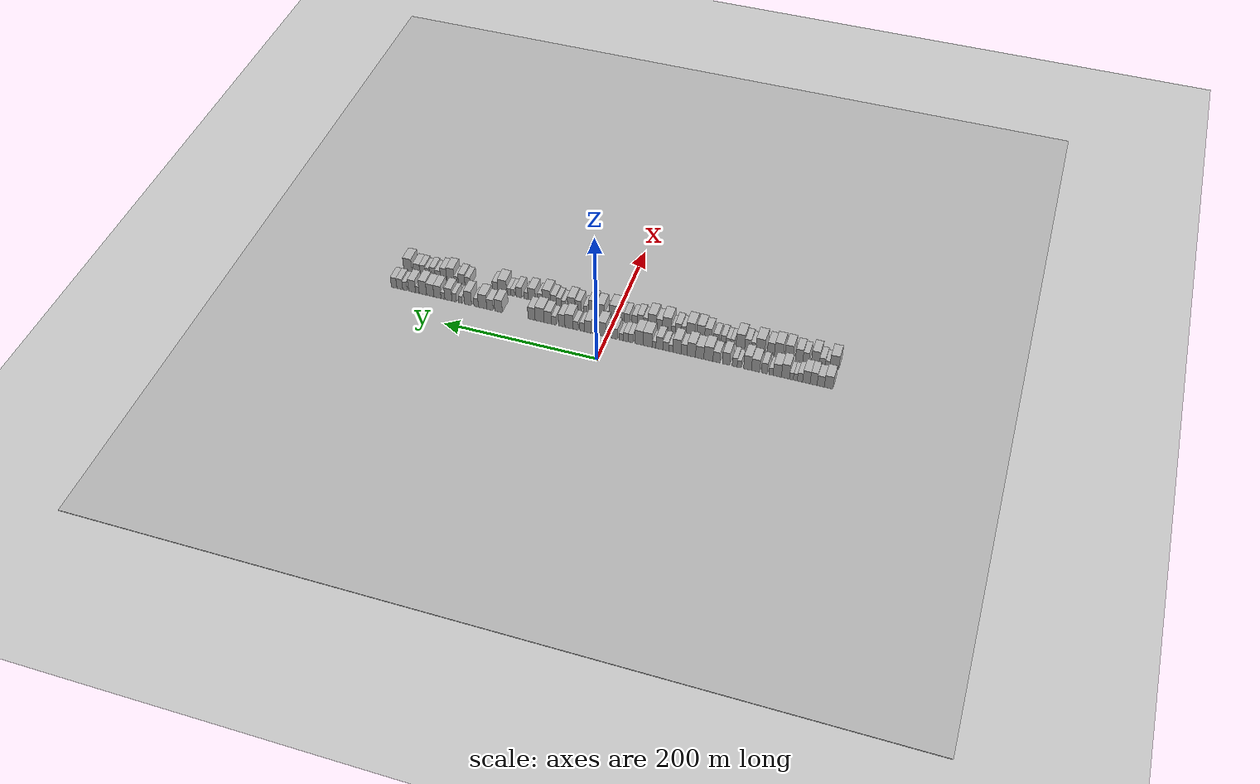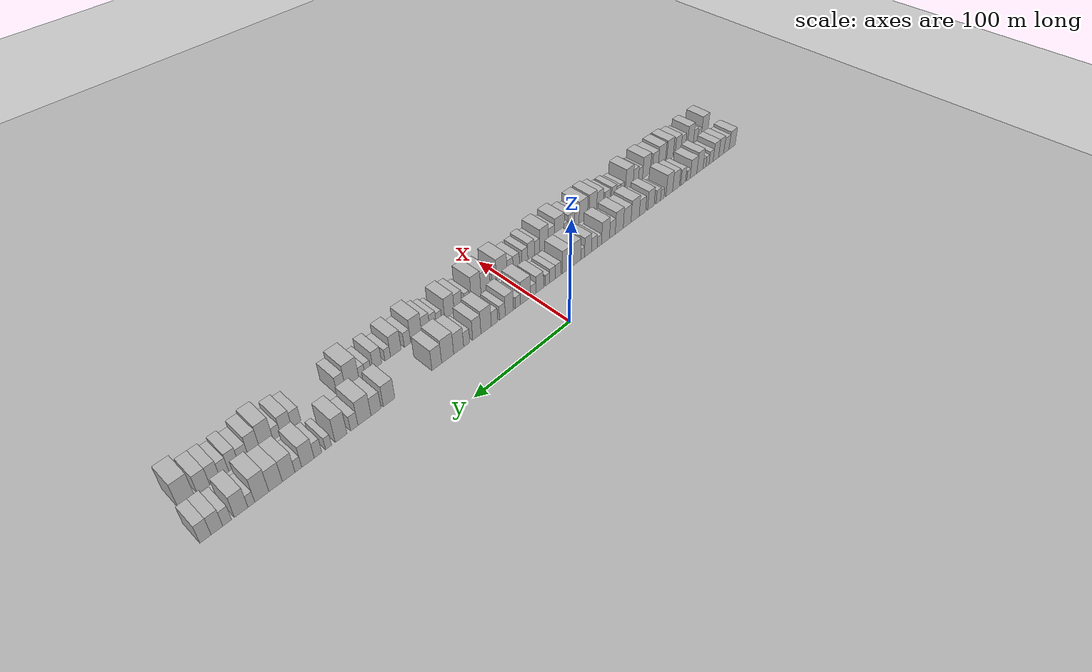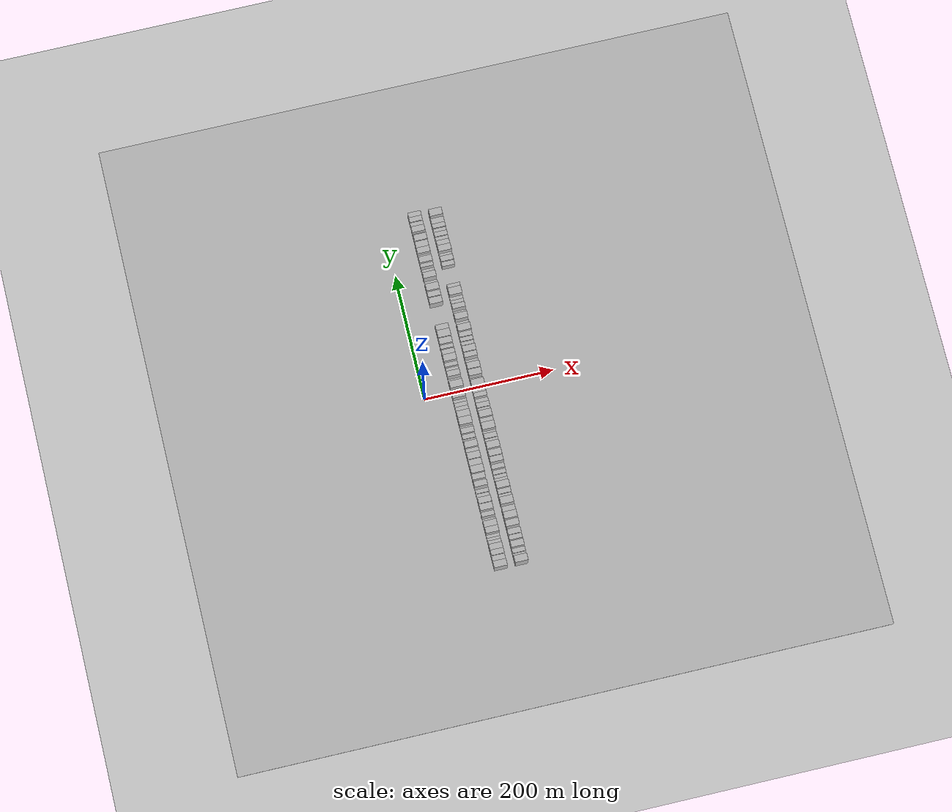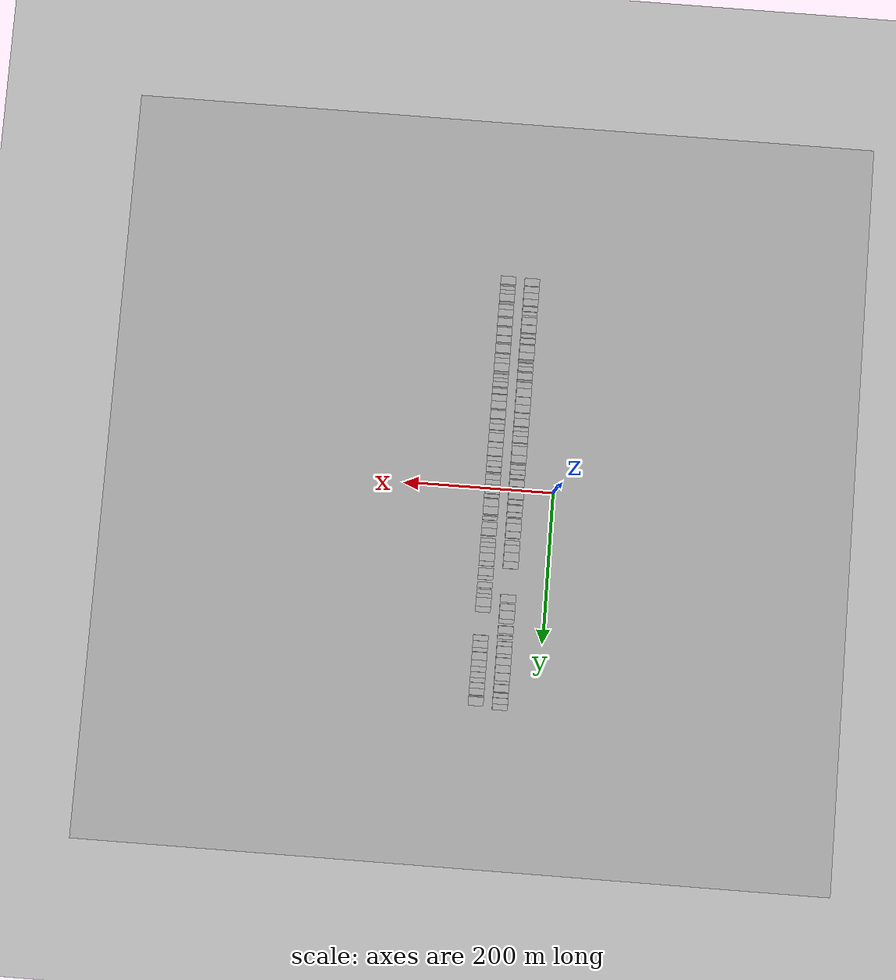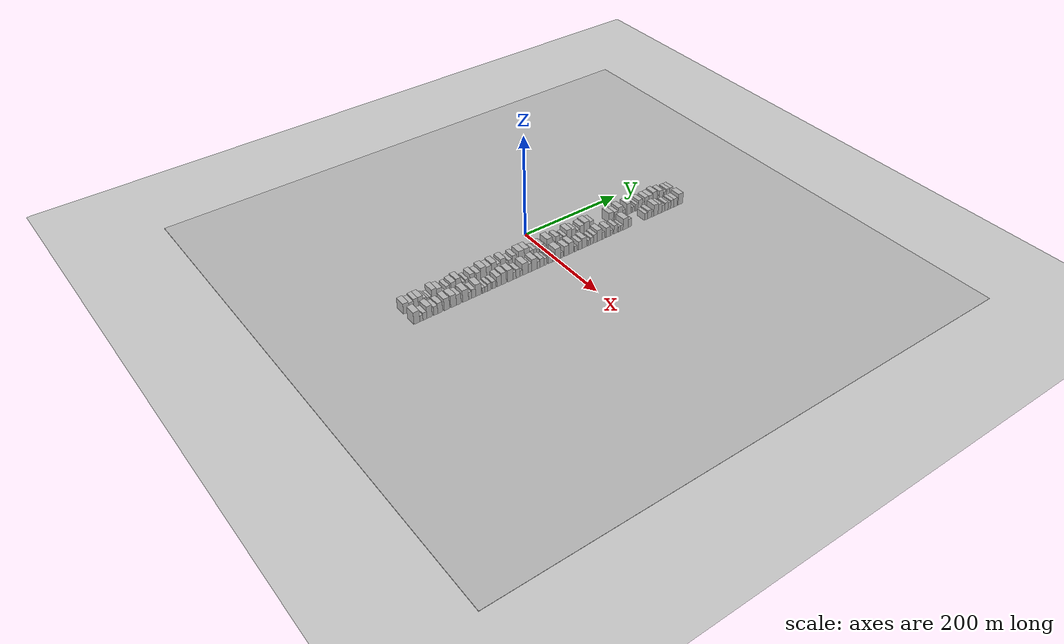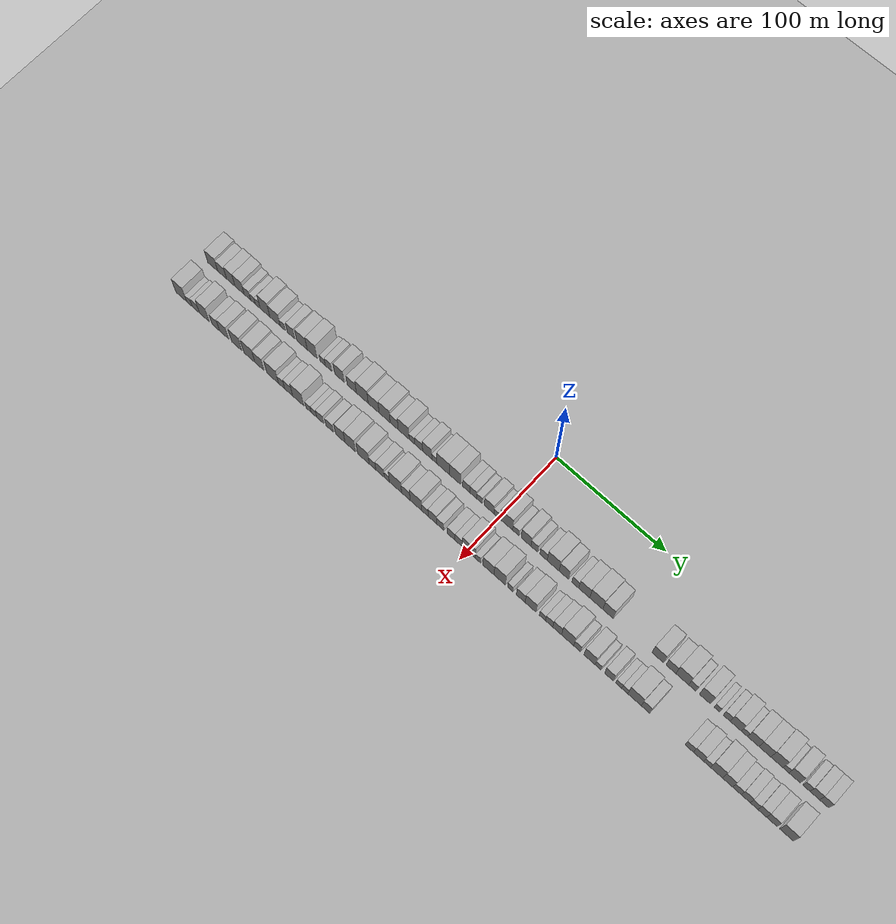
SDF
<?xml version="1.0" encoding="utf-8"?>

<sdf version="1.6">

   <world name="default">

      <gui fullscreen="0">

         <camera name="user_camera">

            <pose>-15 0 4.57585 0 0 0</pose>

            <view_controller>orbit</view_controller>

         </camera>

      </gui>

      <scene>

         <sky>

           <clouds>

             <speed>12</speed>

           </clouds>

         </sky>

         <ambient>0.4 0.4 0.4 1</ambient>

         <background>0.7 0.7 0.7 1</background>

         <shadows>1</shadows>

      </scene>

      <gravity>0 0 -9.8066</gravity>

      <magnetic_field>6e-06 2.3e-05 -4.2e-05</magnetic_field>

      <physics default="0" name="default_physics" type="ode">

         <ode>

            <solver>

               <type>quick</type>

               <iters>10</iters>

               <sor>1.0</sor>

               <use_dynamic_moi_rescaling>0</use_dynamic_moi_rescaling>

            </solver>

            <constraints>

               <cfm>0</cfm>

               <erp>0.2</erp>

               <contact_max_correcting_vel>100</contact_max_correcting_vel>

               <contact_surface_layer>0.001</contact_surface_layer>

            </constraints>

         </ode>

         <max_step_size>0.004</max_step_size>

         <real_time_factor>1</real_time_factor>

         <real_time_update_rate>250</real_time_update_rate>

      </physics>

      <light name="sun" type="directional">

         <cast_shadows>1</cast_shadows>

         <pose>0 0 10 0 0 0</pose>

         <diffuse>0.8 0.8 0.8 1</diffuse>

         <specular>0.2 0.2 0.2 1</specular>

         <attenuation>

            <range>1000</range>

            <constant>0.9</constant>

            <linear>0.01</linear>

            <quadratic>0.001</quadratic>

         </attenuation>

         <direction>-0.5 0.1 -0.9</direction>

      </light>

      <include>

         <name>ground_plane_1</name>

         <uri>model://HANNAS_ground_plane</uri>

         <pose>0 0 0  0 0 0</pose>

      </include>

      <include>

         <name>ground_plane_2</name>

         <uri>model://HANNAS_ground_plane</uri>

         <pose>100 0 0  0 0 0</pose>

      </include>

      <model name="building_1">

         <static>1</static>

         <pose frame="">50.0000 -278.7574 0 0.000000 0.000000 0.000000</pose>

         <link name="link">

            <pose frame="">0 0 10.50 0 0 0</pose>

            <collision name="collision">

               <geometry>

                  <box>

                     <size>20.0000 10.4853 21.0000</size>

                  </box>

               </geometry>

               <max_contacts>10</max_contacts>

               <surface>

                  <contact>

                     <ode/>

                  </contact>

                  <bounce/>

                  <friction>

                     <torsional>

                        <ode/>

                     </torsional>

                     <ode/>

                  </friction>

               </surface>

            </collision>

            <visual name="visual">

               <cast_shadows>0</cast_shadows>

               <geometry>

                  <box>

                     <size>20.0000 10.4853 21.0000</size>

                  </box>

               </geometry>

               <material>

                  <script>

                     <uri>model://HANNAS_wall/materials/scripts</uri>

                     <uri>model://HANNAS_wall/materials/textures</uri>

                     <name>vrc/HANNAS_wall</name>

                  </script>

               </material>

            </visual>

            <self_collide>0</self_collide>

            <enable_wind>0</enable_wind>

            <kinematic>0</kinematic>

         </link>

      </model>

      <model name="building_2">

         <static>1</static>

         <pose frame="">50.0000 -269.0719 0 0.000000 0.000000 0.000000</pose>

         <link name="link">

            <pose frame="">0 0 9.00 0 0 0</pose>

            <collision name="collision">

               <geometry>

                  <box>

                     <size>20.0000 8.8856 18.0000</size>

                  </box>

               </geometry>

               <max_contacts>10</max_contacts>

               <surface>

                  <contact>

                     <ode/>

                  </contact>

                  <bounce/>

                  <friction>

                     <torsional>

                        <ode/>

                     </torsional>

                     <ode/>

                  </friction>

               </surface>

            </collision>

            <visual name="visual">

               <cast_shadows>0</cast_shadows>

               <geometry>

                  <box>

                     <size>20.0000 8.8856 18.0000</size>

                  </box>

               </geometry>

               <material>

                  <script>

                     <uri>model://HANNAS_wall/materials/scripts</uri>

                     <uri>model://HANNAS_wall/materials/textures</uri>

                     <name>vrc/HANNAS_wall</name>

                  </script>

               </material>

            </visual>

            <self_collide>0</self_collide>

            <enable_wind>0</enable_wind>

            <kinematic>0</kinematic>

         </link>

      </model>

      <model name="building_3">

         <static>1</static>

         <pose frame="">50.0000 -260.3548 0 0.000000 0.000000 0.000000</pose>

         <link name="link">

            <pose frame="">0 0 10.50 0 0 0</pose>

            <collision name="collision">

               <geometry>

                  <box>

                     <size>20.0000 8.5487 21.0000</size>

                  </box>

               </geometry>

               <max_contacts>10</max_contacts>

               <surface>

                  <contact>

                     <ode/>

                  </contact>

                  <bounce/>

                  <friction>

                     <torsional>

                        <ode/>

                     </torsional>

                     <ode/>

                  </friction>

               </surface>

            </collision>

            <visual name="visual">

               <cast_shadows>0</cast_shadows>

               <geometry>

                  <box>

                     <size>20.0000 8.5487 21.0000</size>

                  </box>

               </geometry>

               <material>

                  <script>

                     <uri>model://HANNAS_wall/materials/scripts</uri>

                     <uri>model://HANNAS_wall/materials/textures</uri>

                     <name>vrc/HANNAS_wall</name>

                  </script>

               </material>

            </visual>

            <self_collide>0</self_collide>

            <enable_wind>0</enable_wind>

            <kinematic>0</kinematic>

         </link>

      </model>

      <model name="building_4">

         <static>1</static>

         <pose frame="">50.0000 -251.4700 0 0.000000 0.000000 0.000000</pose>

         <link name="link">

            <pose frame="">0 0 10.50 0 0 0</pose>

            <collision name="collision">

               <geometry>

                  <box>

                     <size>20.0000 9.2208 21.0000</size>

                  </box>

               </geometry>

               <max_contacts>10</max_contacts>

               <surface>

                  <contact>

                     <ode/>

                  </contact>

                  <bounce/>

                  <friction>

                     <torsional>

                        <ode/>

                     </torsional>

                     <ode/>

                  </friction>

               </surface>

            </collision>

            <visual name="visual">

               <cast_shadows>0</cast_shadows>

               <geometry>

                  <box>

                     <size>20.0000 9.2208 21.0000</size>

                  </box>

               </geometry>

               <material>

                  <script>

                     <uri>model://HANNAS_wall/materials/scripts</uri>

                     <uri>model://HANNAS_wall/materials/textures</uri>

                     <name>vrc/HANNAS_wall</name>

                  </script>

               </material>

            </visual>

            <self_collide>0</self_collide>

            <enable_wind>0</enable_wind>

            <kinematic>0</kinematic>

         </link>

      </model>

      <model name="building_5">

         <static>1</static>

         <pose frame="">50.0000 -243.5951 0 0.000000 0.000000 0.000000</pose>

         <link name="link">

            <pose frame="">0 0 7.50 0 0 0</pose>

            <collision name="collision">

               <geometry>

                  <box>

                     <size>20.0000 6.5289 15.0000</size>

                  </box>

               </geometry>

               <max_contacts>10</max_contacts>

               <surface>

                  <contact>

                     <ode/>

                  </contact>

                  <bounce/>

                  <friction>

                     <torsional>

                        <ode/>

                     </torsional>

                     <ode/>

                  </friction>

               </surface>

            </collision>

            <visual name="visual">

               <cast_shadows>0</cast_shadows>

               <geometry>

                  <box>

                     <size>20.0000 6.5289 15.0000</size>

                  </box>

               </geometry>

               <material>

                  <script>

                     <uri>model://HANNAS_wall/materials/scripts</uri>

                     <uri>model://HANNAS_wall/materials/textures</uri>

                     <name>vrc/HANNAS_wall</name>

                  </script>

               </material>

            </visual>

            <self_collide>0</self_collide>

            <enable_wind>0</enable_wind>

            <kinematic>0</kinematic>

         </link>

      </model>

      <model name="building_6">

         <static>1</static>

         <pose frame="">50.0000 -237.8679 0 0.000000 0.000000 0.000000</pose>

         <link name="link">

            <pose frame="">0 0 6.00 0 0 0</pose>

            <collision name="collision">

               <geometry>

                  <box>

                     <size>20.0000 4.9256 12.0000</size>

                  </box>

               </geometry>

               <max_contacts>10</max_contacts>

               <surface>

                  <contact>

                     <ode/>

                  </contact>

                  <bounce/>

                  <friction>

                     <torsional>

                        <ode/>

                     </torsional>

                     <ode/>

                  </friction>

               </surface>

            </collision>

            <visual name="visual">

               <cast_shadows>0</cast_shadows>

               <geometry>

                  <box>

                     <size>20.0000 4.9256 12.0000</size>

                  </box>

               </geometry>

               <material>

                  <script>

                     <uri>model://HANNAS_wall/materials/scripts</uri>

                     <uri>model://HANNAS_wall/materials/textures</uri>

                     <name>vrc/HANNAS_wall</name>

                  </script>

               </material>

            </visual>

            <self_collide>0</self_collide>

            <enable_wind>0</enable_wind>

            <kinematic>0</kinematic>

         </link>

      </model>

      <model name="building_7">

         <static>1</static>

         <pose frame="">50.0000 -233.0020 0 0.000000 0.000000 0.000000</pose>

         <link name="link">

            <pose frame="">0 0 6.00 0 0 0</pose>

            <collision name="collision">

               <geometry>

                  <box>

                     <size>20.0000 4.8062 12.0000</size>

                  </box>

               </geometry>

               <max_contacts>10</max_contacts>

               <surface>

                  <contact>

                     <ode/>

                  </contact>

                  <bounce/>

                  <friction>

                     <torsional>

                        <ode/>

                     </torsional>

                     <ode/>

                  </friction>

               </surface>

            </collision>

            <visual name="visual">

               <cast_shadows>0</cast_shadows>

               <geometry>

                  <box>

                     <size>20.0000 4.8062 12.0000</size>

                  </box>

               </geometry>

               <material>

                  <script>

                     <uri>model://HANNAS_wall/materials/scripts</uri>

                     <uri>model://HANNAS_wall/materials/textures</uri>

                     <name>vrc/HANNAS_wall</name>

                  </script>

               </material>

            </visual>

            <self_collide>0</self_collide>

            <enable_wind>0</enable_wind>

            <kinematic>0</kinematic>

         </link>

      </model>

      <model name="building_8">

         <static>1</static>

         <pose frame="">50.0000 -225.7242 0 0.000000 0.000000 0.000000</pose>

         <link name="link">

            <pose frame="">0 0 12.00 0 0 0</pose>

            <collision name="collision">

               <geometry>

                  <box>

                     <size>20.0000 9.7495 24.0000</size>

                  </box>

               </geometry>

               <max_contacts>10</max_contacts>

               <surface>

                  <contact>

                     <ode/>

                  </contact>

                  <bounce/>

                  <friction>

                     <torsional>

                        <ode/>

                     </torsional>

                     <ode/>

                  </friction>

               </surface>

            </collision>

            <visual name="visual">

               <cast_shadows>0</cast_shadows>

               <geometry>

                  <box>

                     <size>20.0000 9.7495 24.0000</size>

                  </box>

               </geometry>

               <material>

                  <script>

                     <uri>model://HANNAS_wall/materials/scripts</uri>

                     <uri>model://HANNAS_wall/materials/textures</uri>

                     <name>vrc/HANNAS_wall</name>

                  </script>

               </material>

            </visual>

            <self_collide>0</self_collide>

            <enable_wind>0</enable_wind>

            <kinematic>0</kinematic>

         </link>

      </model>

      <model name="building_9">

         <static>1</static>

         <pose frame="">50.0000 -215.6198 0 0.000000 0.000000 0.000000</pose>

         <link name="link">

            <pose frame="">0 0 10.50 0 0 0</pose>

            <collision name="collision">

               <geometry>

                  <box>

                     <size>20.0000 10.4592 21.0000</size>

                  </box>

               </geometry>

               <max_contacts>10</max_contacts>

               <surface>

                  <contact>

                     <ode/>

                  </contact>

                  <bounce/>

                  <friction>

                     <torsional>

                        <ode/>

                     </torsional>

                     <ode/>

                  </friction>

               </surface>

            </collision>

            <visual name="visual">

               <cast_shadows>0</cast_shadows>

               <geometry>

                  <box>

                     <size>20.0000 10.4592 21.0000</size>

                  </box>

               </geometry>

               <material>

                  <script>

                     <uri>model://HANNAS_wall/materials/scripts</uri>

                     <uri>model://HANNAS_wall/materials/textures</uri>

                     <name>vrc/HANNAS_wall</name>

                  </script>

               </material>

            </visual>

            <self_collide>0</self_collide>

            <enable_wind>0</enable_wind>

            <kinematic>0</kinematic>

         </link>

      </model>

      <model name="building_10">

         <static>1</static>

         <pose frame="">50.0000 -207.8413 0 0.000000 0.000000 0.000000</pose>

         <link name="link">

            <pose frame="">0 0 6.00 0 0 0</pose>

            <collision name="collision">

               <geometry>

                  <box>

                     <size>20.0000 5.0979 12.0000</size>

                  </box>

               </geometry>

               <max_contacts>10</max_contacts>

               <surface>

                  <contact>

                     <ode/>

                  </contact>

                  <bounce/>

                  <friction>

                     <torsional>

                        <ode/>

                     </torsional>

                     <ode/>

                  </friction>

               </surface>

            </collision>

            <visual name="visual">

               <cast_shadows>0</cast_shadows>

               <geometry>

                  <box>

                     <size>20.0000 5.0979 12.0000</size>

                  </box>

               </geometry>

               <material>

                  <script>

                     <uri>model://HANNAS_wall/materials/scripts</uri>

                     <uri>model://HANNAS_wall/materials/textures</uri>

                     <name>vrc/HANNAS_wall</name>

                  </script>

               </material>

            </visual>

            <self_collide>0</self_collide>

            <enable_wind>0</enable_wind>

            <kinematic>0</kinematic>

         </link>

      </model>

      <model name="building_11">

         <static>1</static>

         <pose frame="">50.0000 -199.5938 0 0.000000 0.000000 0.000000</pose>

         <link name="link">

            <pose frame="">0 0 9.00 0 0 0</pose>

            <collision name="collision">

               <geometry>

                  <box>

                     <size>20.0000 7.3971 18.0000</size>

                  </box>

               </geometry>

               <max_contacts>10</max_contacts>

               <surface>

                  <contact>

                     <ode/>

                  </contact>

                  <bounce/>

                  <friction>

                     <torsional>

                        <ode/>

                     </torsional>

                     <ode/>

                  </friction>

               </surface>

            </collision>

            <visual name="visual">

               <cast_shadows>0</cast_shadows>

               <geometry>

                  <box>

                     <size>20.0000 7.3971 18.0000</size>

                  </box>

               </geometry>

               <material>

                  <script>

                     <uri>model://HANNAS_wall/materials/scripts</uri>

                     <uri>model://HANNAS_wall/materials/textures</uri>

                     <name>vrc/HANNAS_wall</name>

                  </script>

               </material>

            </visual>

            <self_collide>0</self_collide>

            <enable_wind>0</enable_wind>

            <kinematic>0</kinematic>

         </link>

      </model>

      <model name="building_12">

         <static>1</static>

         <pose frame="">50.0000 -188.7349 0 0.000000 0.000000 0.000000</pose>

         <link name="link">

            <pose frame="">0 0 10.50 0 0 0</pose>

            <collision name="collision">

               <geometry>

                  <box>

                     <size>20.0000 10.3207 21.0000</size>

                  </box>

               </geometry>

               <max_contacts>10</max_contacts>

               <surface>

                  <contact>

                     <ode/>

                  </contact>

                  <bounce/>

                  <friction>

                     <torsional>

                        <ode/>

                     </torsional>

                     <ode/>

                  </friction>

               </surface>

            </collision>

            <visual name="visual">

               <cast_shadows>0</cast_shadows>

               <geometry>

                  <box>

                     <size>20.0000 10.3207 21.0000</size>

                  </box>

               </geometry>

               <material>

                  <script>

                     <uri>model://HANNAS_wall/materials/scripts</uri>

                     <uri>model://HANNAS_wall/materials/textures</uri>

                     <name>vrc/HANNAS_wall</name>

                  </script>

               </material>

            </visual>

            <self_collide>0</self_collide>

            <enable_wind>0</enable_wind>

            <kinematic>0</kinematic>

         </link>

      </model>

      <model name="building_13">

         <static>1</static>

         <pose frame="">50.0000 -178.7163 0 0.000000 0.000000 0.000000</pose>

         <link name="link">

            <pose frame="">0 0 12.00 0 0 0</pose>

            <collision name="collision">

               <geometry>

                  <box>

                     <size>20.0000 9.7165 24.0000</size>

                  </box>

               </geometry>

               <max_contacts>10</max_contacts>

               <surface>

                  <contact>

                     <ode/>

                  </contact>

                  <bounce/>

                  <friction>

                     <torsional>

                        <ode/>

                     </torsional>

                     <ode/>

                  </friction>

               </surface>

            </collision>

            <visual name="visual">

               <cast_shadows>0</cast_shadows>

               <geometry>

                  <box>

                     <size>20.0000 9.7165 24.0000</size>

                  </box>

               </geometry>

               <material>

                  <script>

                     <uri>model://HANNAS_wall/materials/scripts</uri>

                     <uri>model://HANNAS_wall/materials/textures</uri>

                     <name>vrc/HANNAS_wall</name>

                  </script>

               </material>

            </visual>

            <self_collide>0</self_collide>

            <enable_wind>0</enable_wind>

            <kinematic>0</kinematic>

         </link>

      </model>

      <model name="building_14">

         <static>1</static>

         <pose frame="">50.0000 -168.2957 0 0.000000 0.000000 0.000000</pose>

         <link name="link">

            <pose frame="">0 0 6.00 0 0 0</pose>

            <collision name="collision">

               <geometry>

                  <box>

                     <size>20.0000 5.1247 12.0000</size>

                  </box>

               </geometry>

               <max_contacts>10</max_contacts>

               <surface>

                  <contact>

                     <ode/>

                  </contact>

                  <bounce/>

                  <friction>

                     <torsional>

                        <ode/>

                     </torsional>

                     <ode/>

                  </friction>

               </surface>

            </collision>

            <visual name="visual">

               <cast_shadows>0</cast_shadows>

               <geometry>

                  <box>

                     <size>20.0000 5.1247 12.0000</size>

                  </box>

               </geometry>

               <material>

                  <script>

                     <uri>model://HANNAS_wall/materials/scripts</uri>

                     <uri>model://HANNAS_wall/materials/textures</uri>

                     <name>vrc/HANNAS_wall</name>

                  </script>

               </material>

            </visual>

            <self_collide>0</self_collide>

            <enable_wind>0</enable_wind>

            <kinematic>0</kinematic>

         </link>

      </model>

      <model name="building_15">

         <static>1</static>

         <pose frame="">50.0000 -162.6026 0 0.000000 0.000000 0.000000</pose>

         <link name="link">

            <pose frame="">0 0 7.50 0 0 0</pose>

            <collision name="collision">

               <geometry>

                  <box>

                     <size>20.0000 6.2617 15.0000</size>

                  </box>

               </geometry>

               <max_contacts>10</max_contacts>

               <surface>

                  <contact>

                     <ode/>

                  </contact>

                  <bounce/>

                  <friction>

                     <torsional>

                        <ode/>

                     </torsional>

                     <ode/>

                  </friction>

               </surface>

            </collision>

            <visual name="visual">

               <cast_shadows>0</cast_shadows>

               <geometry>

                  <box>

                     <size>20.0000 6.2617 15.0000</size>

                  </box>

               </geometry>

               <material>

                  <script>

                     <uri>model://HANNAS_wall/materials/scripts</uri>

                     <uri>model://HANNAS_wall/materials/textures</uri>

                     <name>vrc/HANNAS_wall</name>

                  </script>

               </material>

            </visual>

            <self_collide>0</self_collide>

            <enable_wind>0</enable_wind>

            <kinematic>0</kinematic>

         </link>

      </model>

      <model name="building_16">

         <static>1</static>

         <pose frame="">50.0000 -151.8582 0 0.000000 0.000000 0.000000</pose>

         <link name="link">

            <pose frame="">0 0 10.50 0 0 0</pose>

            <collision name="collision">

               <geometry>

                  <box>

                     <size>20.0000 9.2272 21.0000</size>

                  </box>

               </geometry>

               <max_contacts>10</max_contacts>

               <surface>

                  <contact>

                     <ode/>

                  </contact>

                  <bounce/>

                  <friction>

                     <torsional>

                        <ode/>

                     </torsional>

                     <ode/>

                  </friction>

               </surface>

            </collision>

            <visual name="visual">

               <cast_shadows>0</cast_shadows>

               <geometry>

                  <box>

                     <size>20.0000 9.2272 21.0000</size>

                  </box>

               </geometry>

               <material>

                  <script>

                     <uri>model://HANNAS_wall/materials/scripts</uri>

                     <uri>model://HANNAS_wall/materials/textures</uri>

                     <name>vrc/HANNAS_wall</name>

                  </script>

               </material>

            </visual>

            <self_collide>0</self_collide>

            <enable_wind>0</enable_wind>

            <kinematic>0</kinematic>

         </link>

      </model>

      <model name="building_17">

         <static>1</static>

         <pose frame="">50.0000 -139.7778 0 0.000000 0.000000 0.000000</pose>

         <link name="link">

            <pose frame="">0 0 9.00 0 0 0</pose>

            <collision name="collision">

               <geometry>

                  <box>

                     <size>20.0000 8.9334 18.0000</size>

                  </box>

               </geometry>

               <max_contacts>10</max_contacts>

               <surface>

                  <contact>

                     <ode/>

                  </contact>

                  <bounce/>

                  <friction>

                     <torsional>

                        <ode/>

                     </torsional>

                     <ode/>

                  </friction>

               </surface>

            </collision>

            <visual name="visual">

               <cast_shadows>0</cast_shadows>

               <geometry>

                  <box>

                     <size>20.0000 8.9334 18.0000</size>

                  </box>

               </geometry>

               <material>

                  <script>

                     <uri>model://HANNAS_wall/materials/scripts</uri>

                     <uri>model://HANNAS_wall/materials/textures</uri>

                     <name>vrc/HANNAS_wall</name>

                  </script>

               </material>

            </visual>

            <self_collide>0</self_collide>

            <enable_wind>0</enable_wind>

            <kinematic>0</kinematic>

         </link>

      </model>

      <model name="building_18">

         <static>1</static>

         <pose frame="">50.0000 -129.5712 0 0.000000 0.000000 0.000000</pose>

         <link name="link">

            <pose frame="">0 0 12.00 0 0 0</pose>

            <collision name="collision">

               <geometry>

                  <box>

                     <size>20.0000 11.4799 24.0000</size>

                  </box>

               </geometry>

               <max_contacts>10</max_contacts>

               <surface>

                  <contact>

                     <ode/>

                  </contact>

                  <bounce/>

                  <friction>

                     <torsional>

                        <ode/>

                     </torsional>

                     <ode/>

                  </friction>

               </surface>

            </collision>

            <visual name="visual">

               <cast_shadows>0</cast_shadows>

               <geometry>

                  <box>

                     <size>20.0000 11.4799 24.0000</size>

                  </box>

               </geometry>

               <material>

                  <script>

                     <uri>model://HANNAS_wall/materials/scripts</uri>

                     <uri>model://HANNAS_wall/materials/textures</uri>

                     <name>vrc/HANNAS_wall</name>

                  </script>

               </material>

            </visual>

            <self_collide>0</self_collide>

            <enable_wind>0</enable_wind>

            <kinematic>0</kinematic>

         </link>

      </model>

      <model name="building_19">

         <static>1</static>

         <pose frame="">50.0000 -118.5897 0 0.000000 0.000000 0.000000</pose>

         <link name="link">

            <pose frame="">0 0 10.50 0 0 0</pose>

            <collision name="collision">

               <geometry>

                  <box>

                     <size>20.0000 10.4830 21.0000</size>

                  </box>

               </geometry>

               <max_contacts>10</max_contacts>

               <surface>

                  <contact>

                     <ode/>

                  </contact>

                  <bounce/>

                  <friction>

                     <torsional>

                        <ode/>

                     </torsional>

                     <ode/>

                  </friction>

               </surface>

            </collision>

            <visual name="visual">

               <cast_shadows>0</cast_shadows>

               <geometry>

                  <box>

                     <size>20.0000 10.4830 21.0000</size>

                  </box>

               </geometry>

               <material>

                  <script>

                     <uri>model://HANNAS_wall/materials/scripts</uri>

                     <uri>model://HANNAS_wall/materials/textures</uri>

                     <name>vrc/HANNAS_wall</name>

                  </script>

               </material>

            </visual>

            <self_collide>0</self_collide>

            <enable_wind>0</enable_wind>

            <kinematic>0</kinematic>

         </link>

      </model>

      <model name="building_20">

         <static>1</static>

         <pose frame="">50.0000 -107.9969 0 0.000000 0.000000 0.000000</pose>

         <link name="link">

            <pose frame="">0 0 12.00 0 0 0</pose>

            <collision name="collision">

               <geometry>

                  <box>

                     <size>20.0000 10.7027 24.0000</size>

                  </box>

               </geometry>

               <max_contacts>10</max_contacts>

               <surface>

                  <contact>

                     <ode/>

                  </contact>

                  <bounce/>

                  <friction>

                     <torsional>

                        <ode/>

                     </torsional>

                     <ode/>

                  </friction>

               </surface>

            </collision>

            <visual name="visual">

               <cast_shadows>0</cast_shadows>

               <geometry>

                  <box>

                     <size>20.0000 10.7027 24.0000</size>

                  </box>

               </geometry>

               <material>

                  <script>

                     <uri>model://HANNAS_wall/materials/scripts</uri>

                     <uri>model://HANNAS_wall/materials/textures</uri>

                     <name>vrc/HANNAS_wall</name>

                  </script>

               </material>

            </visual>

            <self_collide>0</self_collide>

            <enable_wind>0</enable_wind>

            <kinematic>0</kinematic>

         </link>

      </model>

      <model name="building_21">

         <static>1</static>

         <pose frame="">50.0000 -98.8273 0 0.000000 0.000000 0.000000</pose>

         <link name="link">

            <pose frame="">0 0 9.00 0 0 0</pose>

            <collision name="collision">

               <geometry>

                  <box>

                     <size>20.0000 7.6364 18.0000</size>

                  </box>

               </geometry>

               <max_contacts>10</max_contacts>

               <surface>

                  <contact>

                     <ode/>

                  </contact>

                  <bounce/>

                  <friction>

                     <torsional>

                        <ode/>

                     </torsional>

                     <ode/>

                  </friction>

               </surface>

            </collision>

            <visual name="visual">

               <cast_shadows>0</cast_shadows>

               <geometry>

                  <box>

                     <size>20.0000 7.6364 18.0000</size>

                  </box>

               </geometry>

               <material>

                  <script>

                     <uri>model://HANNAS_wall/materials/scripts</uri>

                     <uri>model://HANNAS_wall/materials/textures</uri>

                     <name>vrc/HANNAS_wall</name>

                  </script>

               </material>

            </visual>

            <self_collide>0</self_collide>

            <enable_wind>0</enable_wind>

            <kinematic>0</kinematic>

         </link>

      </model>

      <model name="building_22">

         <static>1</static>

         <pose frame="">50.0000 -89.7715 0 0.000000 0.000000 0.000000</pose>

         <link name="link">

            <pose frame="">0 0 12.00 0 0 0</pose>

            <collision name="collision">

               <geometry>

                  <box>

                     <size>20.0000 10.4751 24.0000</size>

                  </box>

               </geometry>

               <max_contacts>10</max_contacts>

               <surface>

                  <contact>

                     <ode/>

                  </contact>

                  <bounce/>

                  <friction>

                     <torsional>

                        <ode/>

                     </torsional>

                     <ode/>

                  </friction>

               </surface>

            </collision>

            <visual name="visual">

               <cast_shadows>0</cast_shadows>

               <geometry>

                  <box>

                     <size>20.0000 10.4751 24.0000</size>

                  </box>

               </geometry>

               <material>

                  <script>

                     <uri>model://HANNAS_wall/materials/scripts</uri>

                     <uri>model://HANNAS_wall/materials/textures</uri>

                     <name>vrc/HANNAS_wall</name>

                  </script>

               </material>

            </visual>

            <self_collide>0</self_collide>

            <enable_wind>0</enable_wind>

            <kinematic>0</kinematic>

         </link>

      </model>

      <model name="building_23">

         <static>1</static>

         <pose frame="">50.0000 -81.7449 0 0.000000 0.000000 0.000000</pose>

         <link name="link">

            <pose frame="">0 0 6.00 0 0 0</pose>

            <collision name="collision">

               <geometry>

                  <box>

                     <size>20.0000 5.5781 12.0000</size>

                  </box>

               </geometry>

               <max_contacts>10</max_contacts>

               <surface>

                  <contact>

                     <ode/>

                  </contact>

                  <bounce/>

                  <friction>

                     <torsional>

                        <ode/>

                     </torsional>

                     <ode/>

                  </friction>

               </surface>

            </collision>

            <visual name="visual">

               <cast_shadows>0</cast_shadows>

               <geometry>

                  <box>

                     <size>20.0000 5.5781 12.0000</size>

                  </box>

               </geometry>

               <material>

                  <script>

                     <uri>model://HANNAS_wall/materials/scripts</uri>

                     <uri>model://HANNAS_wall/materials/textures</uri>

                     <name>vrc/HANNAS_wall</name>

                  </script>

               </material>

            </visual>

            <self_collide>0</self_collide>

            <enable_wind>0</enable_wind>

            <kinematic>0</kinematic>

         </link>

      </model>

      <model name="building_24">

         <static>1</static>

         <pose frame="">50.0000 -75.2791 0 0.000000 0.000000 0.000000</pose>

         <link name="link">

            <pose frame="">0 0 7.50 0 0 0</pose>

            <collision name="collision">

               <geometry>

                  <box>

                     <size>20.0000 7.3536 15.0000</size>

                  </box>

               </geometry>

               <max_contacts>10</max_contacts>

               <surface>

                  <contact>

                     <ode/>

                  </contact>

                  <bounce/>

                  <friction>

                     <torsional>

                        <ode/>

                     </torsional>

                     <ode/>

                  </friction>

               </surface>

            </collision>

            <visual name="visual">

               <cast_shadows>0</cast_shadows>

               <geometry>

                  <box>

                     <size>20.0000 7.3536 15.0000</size>

                  </box>

               </geometry>

               <material>

                  <script>

                     <uri>model://HANNAS_wall/materials/scripts</uri>

                     <uri>model://HANNAS_wall/materials/textures</uri>

                     <name>vrc/HANNAS_wall</name>

                  </script>

               </material>

            </visual>

            <self_collide>0</self_collide>

            <enable_wind>0</enable_wind>

            <kinematic>0</kinematic>

         </link>

      </model>

      <model name="building_25">

         <static>1</static>

         <pose frame="">50.0000 -67.2632 0 0.000000 0.000000 0.000000</pose>

         <link name="link">

            <pose frame="">0 0 10.50 0 0 0</pose>

            <collision name="collision">

               <geometry>

                  <box>

                     <size>20.0000 8.6782 21.0000</size>

                  </box>

               </geometry>

               <max_contacts>10</max_contacts>

               <surface>

                  <contact>

                     <ode/>

                  </contact>

                  <bounce/>

                  <friction>

                     <torsional>

                        <ode/>

                     </torsional>

                     <ode/>

                  </friction>

               </surface>

            </collision>

            <visual name="visual">

               <cast_shadows>0</cast_shadows>

               <geometry>

                  <box>

                     <size>20.0000 8.6782 21.0000</size>

                  </box>

               </geometry>

               <material>

                  <script>

                     <uri>model://HANNAS_wall/materials/scripts</uri>

                     <uri>model://HANNAS_wall/materials/textures</uri>

                     <name>vrc/HANNAS_wall</name>

                  </script>

               </material>

            </visual>

            <self_collide>0</self_collide>

            <enable_wind>0</enable_wind>

            <kinematic>0</kinematic>

         </link>

      </model>

      <model name="building_26">

         <static>1</static>

         <pose frame="">50.0000 -60.4848 0 0.000000 0.000000 0.000000</pose>

         <link name="link">

            <pose frame="">0 0 6.00 0 0 0</pose>

            <collision name="collision">

               <geometry>

                  <box>

                     <size>20.0000 4.8786 12.0000</size>

                  </box>

               </geometry>

               <max_contacts>10</max_contacts>

               <surface>

                  <contact>

                     <ode/>

                  </contact>

                  <bounce/>

                  <friction>

                     <torsional>

                        <ode/>

                     </torsional>

                     <ode/>

                  </friction>

               </surface>

            </collision>

            <visual name="visual">

               <cast_shadows>0</cast_shadows>

               <geometry>

                  <box>

                     <size>20.0000 4.8786 12.0000</size>

                  </box>

               </geometry>

               <material>

                  <script>

                     <uri>model://HANNAS_wall/materials/scripts</uri>

                     <uri>model://HANNAS_wall/materials/textures</uri>

                     <name>vrc/HANNAS_wall</name>

                  </script>

               </material>

            </visual>

            <self_collide>0</self_collide>

            <enable_wind>0</enable_wind>

            <kinematic>0</kinematic>

         </link>

      </model>

      <model name="building_27">

         <static>1</static>

         <pose frame="">50.0000 -52.0567 0 0.000000 0.000000 0.000000</pose>

         <link name="link">

            <pose frame="">0 0 12.00 0 0 0</pose>

            <collision name="collision">

               <geometry>

                  <box>

                     <size>20.0000 11.9777 24.0000</size>

                  </box>

               </geometry>

               <max_contacts>10</max_contacts>

               <surface>

                  <contact>

                     <ode/>

                  </contact>

                  <bounce/>

                  <friction>

                     <torsional>

                        <ode/>

                     </torsional>

                     <ode/>

                  </friction>

               </surface>

            </collision>

            <visual name="visual">

               <cast_shadows>0</cast_shadows>

               <geometry>

                  <box>

                     <size>20.0000 11.9777 24.0000</size>

                  </box>

               </geometry>

               <material>

                  <script>

                     <uri>model://HANNAS_wall/materials/scripts</uri>

                     <uri>model://HANNAS_wall/materials/textures</uri>

                     <name>vrc/HANNAS_wall</name>

                  </script>

               </material>

            </visual>

            <self_collide>0</self_collide>

            <enable_wind>0</enable_wind>

            <kinematic>0</kinematic>

         </link>

      </model>

      <model name="building_28">

         <static>1</static>

         <pose frame="">50.0000 -40.9466 0 0.000000 0.000000 0.000000</pose>

         <link name="link">

            <pose frame="">0 0 12.00 0 0 0</pose>

            <collision name="collision">

               <geometry>

                  <box>

                     <size>20.0000 10.2426 24.0000</size>

                  </box>

               </geometry>

               <max_contacts>10</max_contacts>

               <surface>

                  <contact>

                     <ode/>

                  </contact>

                  <bounce/>

                  <friction>

                     <torsional>

                        <ode/>

                     </torsional>

                     <ode/>

                  </friction>

               </surface>

            </collision>

            <visual name="visual">

               <cast_shadows>0</cast_shadows>

               <geometry>

                  <box>

                     <size>20.0000 10.2426 24.0000</size>

                  </box>

               </geometry>

               <material>

                  <script>

                     <uri>model://HANNAS_wall/materials/scripts</uri>

                     <uri>model://HANNAS_wall/materials/textures</uri>

                     <name>vrc/HANNAS_wall</name>

                  </script>

               </material>

            </visual>

            <self_collide>0</self_collide>

            <enable_wind>0</enable_wind>

            <kinematic>0</kinematic>

         </link>

      </model>

      <model name="building_29">

         <static>1</static>

         <pose frame="">50.0000 -30.5778 0 0.000000 0.000000 0.000000</pose>

         <link name="link">

            <pose frame="">0 0 7.50 0 0 0</pose>

            <collision name="collision">

               <geometry>

                  <box>

                     <size>20.0000 6.4950 15.0000</size>

                  </box>

               </geometry>

               <max_contacts>10</max_contacts>

               <surface>

                  <contact>

                     <ode/>

                  </contact>

                  <bounce/>

                  <friction>

                     <torsional>

                        <ode/>

                     </torsional>

                     <ode/>

                  </friction>

               </surface>

            </collision>

            <visual name="visual">

               <cast_shadows>0</cast_shadows>

               <geometry>

                  <box>

                     <size>20.0000 6.4950 15.0000</size>

                  </box>

               </geometry>

               <material>

                  <script>

                     <uri>model://HANNAS_wall/materials/scripts</uri>

                     <uri>model://HANNAS_wall/materials/textures</uri>

                     <name>vrc/HANNAS_wall</name>

                  </script>

               </material>

            </visual>

            <self_collide>0</self_collide>

            <enable_wind>0</enable_wind>

            <kinematic>0</kinematic>

         </link>

      </model>

      <model name="building_30">

         <static>1</static>

         <pose frame="">50.0000 -24.1028 0 0.000000 0.000000 0.000000</pose>

         <link name="link">

            <pose frame="">0 0 7.50 0 0 0</pose>

            <collision name="collision">

               <geometry>

                  <box>

                     <size>20.0000 6.4550 15.0000</size>

                  </box>

               </geometry>

               <max_contacts>10</max_contacts>

               <surface>

                  <contact>

                     <ode/>

                  </contact>

                  <bounce/>

                  <friction>

                     <torsional>

                        <ode/>

                     </torsional>

                     <ode/>

                  </friction>

               </surface>

            </collision>

            <visual name="visual">

               <cast_shadows>0</cast_shadows>

               <geometry>

                  <box>

                     <size>20.0000 6.4550 15.0000</size>

                  </box>

               </geometry>

               <material>

                  <script>

                     <uri>model://HANNAS_wall/materials/scripts</uri>

                     <uri>model://HANNAS_wall/materials/textures</uri>

                     <name>vrc/HANNAS_wall</name>

                  </script>

               </material>

            </visual>

            <self_collide>0</self_collide>

            <enable_wind>0</enable_wind>

            <kinematic>0</kinematic>

         </link>

      </model>

      <model name="building_31">

         <static>1</static>

         <pose frame="">50.0000 -18.1792 0 0.000000 0.000000 0.000000</pose>

         <link name="link">

            <pose frame="">0 0 6.00 0 0 0</pose>

            <collision name="collision">

               <geometry>

                  <box>

                     <size>20.0000 5.3922 12.0000</size>

                  </box>

               </geometry>

               <max_contacts>10</max_contacts>

               <surface>

                  <contact>

                     <ode/>

                  </contact>

                  <bounce/>

                  <friction>

                     <torsional>

                        <ode/>

                     </torsional>

                     <ode/>

                  </friction>

               </surface>

            </collision>

            <visual name="visual">

               <cast_shadows>0</cast_shadows>

               <geometry>

                  <box>

                     <size>20.0000 5.3922 12.0000</size>

                  </box>

               </geometry>

               <material>

                  <script>

                     <uri>model://HANNAS_wall/materials/scripts</uri>

                     <uri>model://HANNAS_wall/materials/textures</uri>

                     <name>vrc/HANNAS_wall</name>

                  </script>

               </material>

            </visual>

            <self_collide>0</self_collide>

            <enable_wind>0</enable_wind>

            <kinematic>0</kinematic>

         </link>

      </model>

      <model name="building_32">

         <static>1</static>

         <pose frame="">50.0000 -9.0547 0 0.000000 0.000000 0.000000</pose>

         <link name="link">

            <pose frame="">0 0 9.00 0 0 0</pose>

            <collision name="collision">

               <geometry>

                  <box>

                     <size>20.0000 8.8566 18.0000</size>

                  </box>

               </geometry>

               <max_contacts>10</max_contacts>

               <surface>

                  <contact>

                     <ode/>

                  </contact>

                  <bounce/>

                  <friction>

                     <torsional>

                        <ode/>

                     </torsional>

                     <ode/>

                  </friction>

               </surface>

            </collision>

            <visual name="visual">

               <cast_shadows>0</cast_shadows>

               <geometry>

                  <box>

                     <size>20.0000 8.8566 18.0000</size>

                  </box>

               </geometry>

               <material>

                  <script>

                     <uri>model://HANNAS_wall/materials/scripts</uri>

                     <uri>model://HANNAS_wall/materials/textures</uri>

                     <name>vrc/HANNAS_wall</name>

                  </script>

               </material>

            </visual>

            <self_collide>0</self_collide>

            <enable_wind>0</enable_wind>

            <kinematic>0</kinematic>

         </link>

      </model>

      <model name="building_33">

         <static>1</static>

         <pose frame="">50.0000 -1.6798 0 0.000000 0.000000 0.000000</pose>

         <link name="link">

            <pose frame="">0 0 6.00 0 0 0</pose>

            <collision name="collision">

               <geometry>

                  <box>

                     <size>20.0000 5.8933 12.0000</size>

                  </box>

               </geometry>

               <max_contacts>10</max_contacts>

               <surface>

                  <contact>

                     <ode/>

                  </contact>

                  <bounce/>

                  <friction>

                     <torsional>

                        <ode/>

                     </torsional>

                     <ode/>

                  </friction>

               </surface>

            </collision>

            <visual name="visual">

               <cast_shadows>0</cast_shadows>

               <geometry>

                  <box>

                     <size>20.0000 5.8933 12.0000</size>

                  </box>

               </geometry>

               <material>

                  <script>

                     <uri>model://HANNAS_wall/materials/scripts</uri>

                     <uri>model://HANNAS_wall/materials/textures</uri>

                     <name>vrc/HANNAS_wall</name>

                  </script>

               </material>

            </visual>

            <self_collide>0</self_collide>

            <enable_wind>0</enable_wind>

            <kinematic>0</kinematic>

         </link>

      </model>

      <model name="building_34">

         <static>1</static>

         <pose frame="">50.0000 6.9483 0 0.000000 0.000000 0.000000</pose>

         <link name="link">

            <pose frame="">0 0 12.00 0 0 0</pose>

            <collision name="collision">

               <geometry>

                  <box>

                     <size>20.0000 11.3630 24.0000</size>

                  </box>

               </geometry>

               <max_contacts>10</max_contacts>

               <surface>

                  <contact>

                     <ode/>

                  </contact>

                  <bounce/>

                  <friction>

                     <torsional>

                        <ode/>

                     </torsional>

                     <ode/>

                  </friction>

               </surface>

            </collision>

            <visual name="visual">

               <cast_shadows>0</cast_shadows>

               <geometry>

                  <box>

                     <size>20.0000 11.3630 24.0000</size>

                  </box>

               </geometry>

               <material>

                  <script>

                     <uri>model://HANNAS_wall/materials/scripts</uri>

                     <uri>model://HANNAS_wall/materials/textures</uri>

                     <name>vrc/HANNAS_wall</name>

                  </script>

               </material>

            </visual>

            <self_collide>0</self_collide>

            <enable_wind>0</enable_wind>

            <kinematic>0</kinematic>

         </link>

      </model>

      <model name="building_35">

         <static>1</static>

         <pose frame="">50.0000 15.5650 0 0.000000 0.000000 0.000000</pose>

         <link name="link">

            <pose frame="">0 0 6.00 0 0 0</pose>

            <collision name="collision">

               <geometry>

                  <box>

                     <size>20.0000 5.8705 12.0000</size>

                  </box>

               </geometry>

               <max_contacts>10</max_contacts>

               <surface>

                  <contact>

                     <ode/>

                  </contact>

                  <bounce/>

                  <friction>

                     <torsional>

                        <ode/>

                     </torsional>

                     <ode/>

                  </friction>

               </surface>

            </collision>

            <visual name="visual">

               <cast_shadows>0</cast_shadows>

               <geometry>

                  <box>

                     <size>20.0000 5.8705 12.0000</size>

                  </box>

               </geometry>

               <material>

                  <script>

                     <uri>model://HANNAS_wall/materials/scripts</uri>

                     <uri>model://HANNAS_wall/materials/textures</uri>

                     <name>vrc/HANNAS_wall</name>

                  </script>

               </material>

            </visual>

            <self_collide>0</self_collide>

            <enable_wind>0</enable_wind>

            <kinematic>0</kinematic>

         </link>

      </model>

      <model name="building_36">

         <static>1</static>

         <pose frame="">50.0000 24.9754 0 0.000000 0.000000 0.000000</pose>

         <link name="link">

            <pose frame="">0 0 10.50 0 0 0</pose>

            <collision name="collision">

               <geometry>

                  <box>

                     <size>20.0000 8.9502 21.0000</size>

                  </box>

               </geometry>

               <max_contacts>10</max_contacts>

               <surface>

                  <contact>

                     <ode/>

                  </contact>

                  <bounce/>

                  <friction>

                     <torsional>

                        <ode/>

                     </torsional>

                     <ode/>

                  </friction>

               </surface>

            </collision>

            <visual name="visual">

               <cast_shadows>0</cast_shadows>

               <geometry>

                  <box>

                     <size>20.0000 8.9502 21.0000</size>

                  </box>

               </geometry>

               <material>

                  <script>

                     <uri>model://HANNAS_wall/materials/scripts</uri>

                     <uri>model://HANNAS_wall/materials/textures</uri>

                     <name>vrc/HANNAS_wall</name>

                  </script>

               </material>

            </visual>

            <self_collide>0</self_collide>

            <enable_wind>0</enable_wind>

            <kinematic>0</kinematic>

         </link>

      </model>

      <model name="building_37">

         <static>1</static>

         <pose frame="">50.0000 32.5412 0 0.000000 0.000000 0.000000</pose>

         <link name="link">

            <pose frame="">0 0 7.50 0 0 0</pose>

            <collision name="collision">

               <geometry>

                  <box>

                     <size>20.0000 6.1814 15.0000</size>

                  </box>

               </geometry>

               <max_contacts>10</max_contacts>

               <surface>

                  <contact>

                     <ode/>

                  </contact>

                  <bounce/>

                  <friction>

                     <torsional>

                        <ode/>

                     </torsional>

                     <ode/>

                  </friction>

               </surface>

            </collision>

            <visual name="visual">

               <cast_shadows>0</cast_shadows>

               <geometry>

                  <box>

                     <size>20.0000 6.1814 15.0000</size>

                  </box>

               </geometry>

               <material>

                  <script>

                     <uri>model://HANNAS_wall/materials/scripts</uri>

                     <uri>model://HANNAS_wall/materials/textures</uri>

                     <name>vrc/HANNAS_wall</name>

                  </script>

               </material>

            </visual>

            <self_collide>0</self_collide>

            <enable_wind>0</enable_wind>

            <kinematic>0</kinematic>

         </link>

      </model>

      <model name="building_38">

         <static>1</static>

         <pose frame="">50.0000 40.9875 0 0.000000 0.000000 0.000000</pose>

         <link name="link">

            <pose frame="">0 0 7.50 0 0 0</pose>

            <collision name="collision">

               <geometry>

                  <box>

                     <size>20.0000 6.7112 15.0000</size>

                  </box>

               </geometry>

               <max_contacts>10</max_contacts>

               <surface>

                  <contact>

                     <ode/>

                  </contact>

                  <bounce/>

                  <friction>

                     <torsional>

                        <ode/>

                     </torsional>

                     <ode/>

                  </friction>

               </surface>

            </collision>

            <visual name="visual">

               <cast_shadows>0</cast_shadows>

               <geometry>

                  <box>

                     <size>20.0000 6.7112 15.0000</size>

                  </box>

               </geometry>

               <material>

                  <script>

                     <uri>model://HANNAS_wall/materials/scripts</uri>

                     <uri>model://HANNAS_wall/materials/textures</uri>

                     <name>vrc/HANNAS_wall</name>

                  </script>

               </material>

            </visual>

            <self_collide>0</self_collide>

            <enable_wind>0</enable_wind>

            <kinematic>0</kinematic>

         </link>

      </model>

      <model name="building_39">

         <static>1</static>

         <pose frame="">50.0000 49.7441 0 0.000000 0.000000 0.000000</pose>

         <link name="link">

            <pose frame="">0 0 12.00 0 0 0</pose>

            <collision name="collision">

               <geometry>

                  <box>

                     <size>20.0000 10.8022 24.0000</size>

                  </box>

               </geometry>

               <max_contacts>10</max_contacts>

               <surface>

                  <contact>

                     <ode/>

                  </contact>

                  <bounce/>

                  <friction>

                     <torsional>

                        <ode/>

                     </torsional>

                     <ode/>

                  </friction>

               </surface>

            </collision>

            <visual name="visual">

               <cast_shadows>0</cast_shadows>

               <geometry>

                  <box>

                     <size>20.0000 10.8022 24.0000</size>

                  </box>

               </geometry>

               <material>

                  <script>

                     <uri>model://HANNAS_wall/materials/scripts</uri>

                     <uri>model://HANNAS_wall/materials/textures</uri>

                     <name>vrc/HANNAS_wall</name>

                  </script>

               </material>

            </visual>

            <self_collide>0</self_collide>

            <enable_wind>0</enable_wind>

            <kinematic>0</kinematic>

         </link>

      </model>

      <model name="building_40">

         <static>1</static>

         <pose frame="">50.0000 59.4152 0 0.000000 0.000000 0.000000</pose>

         <link name="link">

            <pose frame="">0 0 10.50 0 0 0</pose>

            <collision name="collision">

               <geometry>

                  <box>

                     <size>20.0000 8.5400 21.0000</size>

                  </box>

               </geometry>

               <max_contacts>10</max_contacts>

               <surface>

                  <contact>

                     <ode/>

                  </contact>

                  <bounce/>

                  <friction>

                     <torsional>

                        <ode/>

                     </torsional>

                     <ode/>

                  </friction>

               </surface>

            </collision>

            <visual name="visual">

               <cast_shadows>0</cast_shadows>

               <geometry>

                  <box>

                     <size>20.0000 8.5400 21.0000</size>

                  </box>

               </geometry>

               <material>

                  <script>

                     <uri>model://HANNAS_wall/materials/scripts</uri>

                     <uri>model://HANNAS_wall/materials/textures</uri>

                     <name>vrc/HANNAS_wall</name>

                  </script>

               </material>

            </visual>

            <self_collide>0</self_collide>

            <enable_wind>0</enable_wind>

            <kinematic>0</kinematic>

         </link>

      </model>

      <model name="building_41">

         <static>1</static>

         <pose frame="">50.0000 69.7867 0 0.000000 0.000000 0.000000</pose>

         <link name="link">

            <pose frame="">0 0 7.50 0 0 0</pose>

            <collision name="collision">

               <geometry>

                  <box>

                     <size>20.0000 6.2029 15.0000</size>

                  </box>

               </geometry>

               <max_contacts>10</max_contacts>

               <surface>

                  <contact>

                     <ode/>

                  </contact>

                  <bounce/>

                  <friction>

                     <torsional>

                        <ode/>

                     </torsional>

                     <ode/>

                  </friction>

               </surface>

            </collision>

            <visual name="visual">

               <cast_shadows>0</cast_shadows>

               <geometry>

                  <box>

                     <size>20.0000 6.2029 15.0000</size>

                  </box>

               </geometry>

               <material>

                  <script>

                     <uri>model://HANNAS_wall/materials/scripts</uri>

                     <uri>model://HANNAS_wall/materials/textures</uri>

                     <name>vrc/HANNAS_wall</name>

                  </script>

               </material>

            </visual>

            <self_collide>0</self_collide>

            <enable_wind>0</enable_wind>

            <kinematic>0</kinematic>

         </link>

      </model>

      <model name="building_42">

         <static>1</static>

         <pose frame="">50.0000 77.8425 0 0.000000 0.000000 0.000000</pose>

         <link name="link">

            <pose frame="">0 0 10.50 0 0 0</pose>

            <collision name="collision">

               <geometry>

                  <box>

                     <size>20.0000 9.9086 21.0000</size>

                  </box>

               </geometry>

               <max_contacts>10</max_contacts>

               <surface>

                  <contact>

                     <ode/>

                  </contact>

                  <bounce/>

                  <friction>

                     <torsional>

                        <ode/>

                     </torsional>

                     <ode/>

                  </friction>

               </surface>

            </collision>

            <visual name="visual">

               <cast_shadows>0</cast_shadows>

               <geometry>

                  <box>

                     <size>20.0000 9.9086 21.0000</size>

                  </box>

               </geometry>

               <material>

                  <script>

                     <uri>model://HANNAS_wall/materials/scripts</uri>

                     <uri>model://HANNAS_wall/materials/textures</uri>

                     <name>vrc/HANNAS_wall</name>

                  </script>

               </material>

            </visual>

            <self_collide>0</self_collide>

            <enable_wind>0</enable_wind>

            <kinematic>0</kinematic>

         </link>

      </model>

      <model name="building_43">

         <static>1</static>

         <pose frame="">50.0000 88.6916 0 0.000000 0.000000 0.000000</pose>

         <link name="link">

            <pose frame="">0 0 12.00 0 0 0</pose>

            <collision name="collision">

               <geometry>

                  <box>

                     <size>20.0000 11.7896 24.0000</size>

                  </box>

               </geometry>

               <max_contacts>10</max_contacts>

               <surface>

                  <contact>

                     <ode/>

                  </contact>

                  <bounce/>

                  <friction>

                     <torsional>

                        <ode/>

                     </torsional>

                     <ode/>

                  </friction>

               </surface>

            </collision>

            <visual name="visual">

               <cast_shadows>0</cast_shadows>

               <geometry>

                  <box>

                     <size>20.0000 11.7896 24.0000</size>

                  </box>

               </geometry>

               <material>

                  <script>

                     <uri>model://HANNAS_wall/materials/scripts</uri>

                     <uri>model://HANNAS_wall/materials/textures</uri>

                     <name>vrc/HANNAS_wall</name>

                  </script>

               </material>

            </visual>

            <self_collide>0</self_collide>

            <enable_wind>0</enable_wind>

            <kinematic>0</kinematic>

         </link>

      </model>

      <model name="building_44">

         <static>1</static>

         <pose frame="">50.0000 99.2791 0 0.000000 0.000000 0.000000</pose>

         <link name="link">

            <pose frame="">0 0 10.50 0 0 0</pose>

            <collision name="collision">

               <geometry>

                  <box>

                     <size>20.0000 9.3855 21.0000</size>

                  </box>

               </geometry>

               <max_contacts>10</max_contacts>

               <surface>

                  <contact>

                     <ode/>

                  </contact>

                  <bounce/>

                  <friction>

                     <torsional>

                        <ode/>

                     </torsional>

                     <ode/>

                  </friction>

               </surface>

            </collision>

            <visual name="visual">

               <cast_shadows>0</cast_shadows>

               <geometry>

                  <box>

                     <size>20.0000 9.3855 21.0000</size>

                  </box>

               </geometry>

               <material>

                  <script>

                     <uri>model://HANNAS_wall/materials/scripts</uri>

                     <uri>model://HANNAS_wall/materials/textures</uri>

                     <name>vrc/HANNAS_wall</name>

                  </script>

               </material>

            </visual>

            <self_collide>0</self_collide>

            <enable_wind>0</enable_wind>

            <kinematic>0</kinematic>

         </link>

      </model>

      <model name="building_45">

         <static>1</static>

         <pose frame="">50.0000 143.3644 0 0.000000 0.000000 0.000000</pose>

         <link name="link">

            <pose frame="">0 0 10.50 0 0 0</pose>

            <collision name="collision">

               <geometry>

                  <box>

                     <size>20.0000 10.2617 21.0000</size>

                  </box>

               </geometry>

               <max_contacts>10</max_contacts>

               <surface>

                  <contact>

                     <ode/>

                  </contact>

                  <bounce/>

                  <friction>

                     <torsional>

                        <ode/>

                     </torsional>

                     <ode/>

                  </friction>

               </surface>

            </collision>

            <visual name="visual">

               <cast_shadows>0</cast_shadows>

               <geometry>

                  <box>

                     <size>20.0000 10.2617 21.0000</size>

                  </box>

               </geometry>

               <material>

                  <script>

                     <uri>model://HANNAS_wall/materials/scripts</uri>

                     <uri>model://HANNAS_wall/materials/textures</uri>

                     <name>vrc/HANNAS_wall</name>

                  </script>

               </material>

            </visual>

            <self_collide>0</self_collide>

            <enable_wind>0</enable_wind>

            <kinematic>0</kinematic>

         </link>

      </model>

      <model name="building_46">

         <static>1</static>

         <pose frame="">50.0000 154.8397 0 0.000000 0.000000 0.000000</pose>

         <link name="link">

            <pose frame="">0 0 9.00 0 0 0</pose>

            <collision name="collision">

               <geometry>

                  <box>

                     <size>20.0000 8.6888 18.0000</size>

                  </box>

               </geometry>

               <max_contacts>10</max_contacts>

               <surface>

                  <contact>

                     <ode/>

                  </contact>

                  <bounce/>

                  <friction>

                     <torsional>

                        <ode/>

                     </torsional>

                     <ode/>

                  </friction>

               </surface>

            </collision>

            <visual name="visual">

               <cast_shadows>0</cast_shadows>

               <geometry>

                  <box>

                     <size>20.0000 8.6888 18.0000</size>

                  </box>

               </geometry>

               <material>

                  <script>

                     <uri>model://HANNAS_wall/materials/scripts</uri>

                     <uri>model://HANNAS_wall/materials/textures</uri>

                     <name>vrc/HANNAS_wall</name>

                  </script>

               </material>

            </visual>

            <self_collide>0</self_collide>

            <enable_wind>0</enable_wind>

            <kinematic>0</kinematic>

         </link>

      </model>

      <model name="building_47">

         <static>1</static>

         <pose frame="">50.0000 164.7702 0 0.000000 0.000000 0.000000</pose>

         <link name="link">

            <pose frame="">0 0 12.00 0 0 0</pose>

            <collision name="collision">

               <geometry>

                  <box>

                     <size>20.0000 11.1723 24.0000</size>

                  </box>

               </geometry>

               <max_contacts>10</max_contacts>

               <surface>

                  <contact>

                     <ode/>

                  </contact>

                  <bounce/>

                  <friction>

                     <torsional>

                        <ode/>

                     </torsional>

                     <ode/>

                  </friction>

               </surface>

            </collision>

            <visual name="visual">

               <cast_shadows>0</cast_shadows>

               <geometry>

                  <box>

                     <size>20.0000 11.1723 24.0000</size>

                  </box>

               </geometry>

               <material>

                  <script>

                     <uri>model://HANNAS_wall/materials/scripts</uri>

                     <uri>model://HANNAS_wall/materials/textures</uri>

                     <name>vrc/HANNAS_wall</name>

                  </script>

               </material>

            </visual>

            <self_collide>0</self_collide>

            <enable_wind>0</enable_wind>

            <kinematic>0</kinematic>

         </link>

      </model>

      <model name="building_48">

         <static>1</static>

         <pose frame="">50.0000 173.4471 0 0.000000 0.000000 0.000000</pose>

         <link name="link">

            <pose frame="">0 0 7.50 0 0 0</pose>

            <collision name="collision">

               <geometry>

                  <box>

                     <size>20.0000 6.1817 15.0000</size>

                  </box>

               </geometry>

               <max_contacts>10</max_contacts>

               <surface>

                  <contact>

                     <ode/>

                  </contact>

                  <bounce/>

                  <friction>

                     <torsional>

                        <ode/>

                     </torsional>

                     <ode/>

                  </friction>

               </surface>

            </collision>

            <visual name="visual">

               <cast_shadows>0</cast_shadows>

               <geometry>

                  <box>

                     <size>20.0000 6.1817 15.0000</size>

                  </box>

               </geometry>

               <material>

                  <script>

                     <uri>model://HANNAS_wall/materials/scripts</uri>

                     <uri>model://HANNAS_wall/materials/textures</uri>

                     <name>vrc/HANNAS_wall</name>

                  </script>

               </material>

            </visual>

            <self_collide>0</self_collide>

            <enable_wind>0</enable_wind>

            <kinematic>0</kinematic>

         </link>

      </model>

      <model name="building_49">

         <static>1</static>

         <pose frame="">50.0000 184.4023 0 0.000000 0.000000 0.000000</pose>

         <link name="link">

            <pose frame="">0 0 12.00 0 0 0</pose>

            <collision name="collision">

               <geometry>

                  <box>

                     <size>20.0000 9.7286 24.0000</size>

                  </box>

               </geometry>

               <max_contacts>10</max_contacts>

               <surface>

                  <contact>

                     <ode/>

                  </contact>

                  <bounce/>

                  <friction>

                     <torsional>

                        <ode/>

                     </torsional>

                     <ode/>

                  </friction>

               </surface>

            </collision>

            <visual name="visual">

               <cast_shadows>0</cast_shadows>

               <geometry>

                  <box>

                     <size>20.0000 9.7286 24.0000</size>

                  </box>

               </geometry>

               <material>

                  <script>

                     <uri>model://HANNAS_wall/materials/scripts</uri>

                     <uri>model://HANNAS_wall/materials/textures</uri>

                     <name>vrc/HANNAS_wall</name>

                  </script>

               </material>

            </visual>

            <self_collide>0</self_collide>

            <enable_wind>0</enable_wind>

            <kinematic>0</kinematic>

         </link>

      </model>

      <model name="building_50">

         <static>1</static>

         <pose frame="">50.0000 194.6865 0 0.000000 0.000000 0.000000</pose>

         <link name="link">

            <pose frame="">0 0 6.00 0 0 0</pose>

            <collision name="collision">

               <geometry>

                  <box>

                     <size>20.0000 4.8399 12.0000</size>

                  </box>

               </geometry>

               <max_contacts>10</max_contacts>

               <surface>

                  <contact>

                     <ode/>

                  </contact>

                  <bounce/>

                  <friction>

                     <torsional>

                        <ode/>

                     </torsional>

                     <ode/>

                  </friction>

               </surface>

            </collision>

            <visual name="visual">

               <cast_shadows>0</cast_shadows>

               <geometry>

                  <box>

                     <size>20.0000 4.8399 12.0000</size>

                  </box>

               </geometry>

               <material>

                  <script>

                     <uri>model://HANNAS_wall/materials/scripts</uri>

                     <uri>model://HANNAS_wall/materials/textures</uri>

                     <name>vrc/HANNAS_wall</name>

                  </script>

               </material>

            </visual>

            <self_collide>0</self_collide>

            <enable_wind>0</enable_wind>

            <kinematic>0</kinematic>

         </link>

      </model>

      <model name="building_51">

         <static>1</static>

         <pose frame="">50.0000 203.1136 0 0.000000 0.000000 0.000000</pose>

         <link name="link">

            <pose frame="">0 0 7.50 0 0 0</pose>

            <collision name="collision">

               <geometry>

                  <box>

                     <size>20.0000 6.0143 15.0000</size>

                  </box>

               </geometry>

               <max_contacts>10</max_contacts>

               <surface>

                  <contact>

                     <ode/>

                  </contact>

                  <bounce/>

                  <friction>

                     <torsional>

                        <ode/>

                     </torsional>

                     <ode/>

                  </friction>

               </surface>

            </collision>

            <visual name="visual">

               <cast_shadows>0</cast_shadows>

               <geometry>

                  <box>

                     <size>20.0000 6.0143 15.0000</size>

                  </box>

               </geometry>

               <material>

                  <script>

                     <uri>model://HANNAS_wall/materials/scripts</uri>

                     <uri>model://HANNAS_wall/materials/textures</uri>

                     <name>vrc/HANNAS_wall</name>

                  </script>

               </material>

            </visual>

            <self_collide>0</self_collide>

            <enable_wind>0</enable_wind>

            <kinematic>0</kinematic>

         </link>

      </model>

      <model name="building_52">

         <static>1</static>

         <pose frame="">50.0000 210.9976 0 0.000000 0.000000 0.000000</pose>

         <link name="link">

            <pose frame="">0 0 10.50 0 0 0</pose>

            <collision name="collision">

               <geometry>

                  <box>

                     <size>20.0000 9.7535 21.0000</size>

                  </box>

               </geometry>

               <max_contacts>10</max_contacts>

               <surface>

                  <contact>

                     <ode/>

                  </contact>

                  <bounce/>

                  <friction>

                     <torsional>

                        <ode/>

                     </torsional>

                     <ode/>

                  </friction>

               </surface>

            </collision>

            <visual name="visual">

               <cast_shadows>0</cast_shadows>

               <geometry>

                  <box>

                     <size>20.0000 9.7535 21.0000</size>

                  </box>

               </geometry>

               <material>

                  <script>

                     <uri>model://HANNAS_wall/materials/scripts</uri>

                     <uri>model://HANNAS_wall/materials/textures</uri>

                     <name>vrc/HANNAS_wall</name>

                  </script>

               </material>

            </visual>

            <self_collide>0</self_collide>

            <enable_wind>0</enable_wind>

            <kinematic>0</kinematic>

         </link>

      </model>

      <model name="building_53">

         <static>1</static>

         <pose frame="">50.0000 218.4777 0 0.000000 0.000000 0.000000</pose>

         <link name="link">

            <pose frame="">0 0 6.00 0 0 0</pose>

            <collision name="collision">

               <geometry>

                  <box>

                     <size>20.0000 5.2067 12.0000</size>

                  </box>

               </geometry>

               <max_contacts>10</max_contacts>

               <surface>

                  <contact>

                     <ode/>

                  </contact>

                  <bounce/>

                  <friction>

                     <torsional>

                        <ode/>

                     </torsional>

                     <ode/>

                  </friction>

               </surface>

            </collision>

            <visual name="visual">

               <cast_shadows>0</cast_shadows>

               <geometry>

                  <box>

                     <size>20.0000 5.2067 12.0000</size>

                  </box>

               </geometry>

               <material>

                  <script>

                     <uri>model://HANNAS_wall/materials/scripts</uri>

                     <uri>model://HANNAS_wall/materials/textures</uri>

                     <name>vrc/HANNAS_wall</name>

                  </script>

               </material>

            </visual>

            <self_collide>0</self_collide>

            <enable_wind>0</enable_wind>

            <kinematic>0</kinematic>

         </link>

      </model>

      <model name="building_54">

         <static>1</static>

         <pose frame="">50.0000 225.8662 0 0.000000 0.000000 0.000000</pose>

         <link name="link">

            <pose frame="">0 0 10.50 0 0 0</pose>

            <collision name="collision">

               <geometry>

                  <box>

                     <size>20.0000 9.5703 21.0000</size>

                  </box>

               </geometry>

               <max_contacts>10</max_contacts>

               <surface>

                  <contact>

                     <ode/>

                  </contact>

                  <bounce/>

                  <friction>

                     <torsional>

                        <ode/>

                     </torsional>

                     <ode/>

                  </friction>

               </surface>

            </collision>

            <visual name="visual">

               <cast_shadows>0</cast_shadows>

               <geometry>

                  <box>

                     <size>20.0000 9.5703 21.0000</size>

                  </box>

               </geometry>

               <material>

                  <script>

                     <uri>model://HANNAS_wall/materials/scripts</uri>

                     <uri>model://HANNAS_wall/materials/textures</uri>

                     <name>vrc/HANNAS_wall</name>

                  </script>

               </material>

            </visual>

            <self_collide>0</self_collide>

            <enable_wind>0</enable_wind>

            <kinematic>0</kinematic>

         </link>

      </model>

      <model name="building_55">

         <static>1</static>

         <pose frame="">50.0000 235.6811 0 0.000000 0.000000 0.000000</pose>

         <link name="link">

            <pose frame="">0 0 10.50 0 0 0</pose>

            <collision name="collision">

               <geometry>

                  <box>

                     <size>20.0000 10.0596 21.0000</size>

                  </box>

               </geometry>

               <max_contacts>10</max_contacts>

               <surface>

                  <contact>

                     <ode/>

                  </contact>

                  <bounce/>

                  <friction>

                     <torsional>

                        <ode/>

                     </torsional>

                     <ode/>

                  </friction>

               </surface>

            </collision>

            <visual name="visual">

               <cast_shadows>0</cast_shadows>

               <geometry>

                  <box>

                     <size>20.0000 10.0596 21.0000</size>

                  </box>

               </geometry>

               <material>

                  <script>

                     <uri>model://HANNAS_wall/materials/scripts</uri>

                     <uri>model://HANNAS_wall/materials/textures</uri>

                     <name>vrc/HANNAS_wall</name>

                  </script>

               </material>

            </visual>

            <self_collide>0</self_collide>

            <enable_wind>0</enable_wind>

            <kinematic>0</kinematic>

         </link>

      </model>

      <model name="building_56">

         <static>1</static>

         <pose frame="">50.0000 245.8438 0 0.000000 0.000000 0.000000</pose>

         <link name="link">

            <pose frame="">0 0 12.00 0 0 0</pose>

            <collision name="collision">

               <geometry>

                  <box>

                     <size>20.0000 10.2658 24.0000</size>

                  </box>

               </geometry>

               <max_contacts>10</max_contacts>

               <surface>

                  <contact>

                     <ode/>

                  </contact>

                  <bounce/>

                  <friction>

                     <torsional>

                        <ode/>

                     </torsional>

                     <ode/>

                  </friction>

               </surface>

            </collision>

            <visual name="visual">

               <cast_shadows>0</cast_shadows>

               <geometry>

                  <box>

                     <size>20.0000 10.2658 24.0000</size>

                  </box>

               </geometry>

               <material>

                  <script>

                     <uri>model://HANNAS_wall/materials/scripts</uri>

                     <uri>model://HANNAS_wall/materials/textures</uri>

                     <name>vrc/HANNAS_wall</name>

                  </script>

               </material>

            </visual>

            <self_collide>0</self_collide>

            <enable_wind>0</enable_wind>

            <kinematic>0</kinematic>

         </link>

      </model>

      <model name="building_57">

         <static>1</static>

         <pose frame="">50.0000 253.4522 0 0.000000 0.000000 0.000000</pose>

         <link name="link">

            <pose frame="">0 0 6.00 0 0 0</pose>

            <collision name="collision">

               <geometry>

                  <box>

                     <size>20.0000 4.9509 12.0000</size>

                  </box>

               </geometry>

               <max_contacts>10</max_contacts>

               <surface>

                  <contact>

                     <ode/>

                  </contact>

                  <bounce/>

                  <friction>

                     <torsional>

                        <ode/>

                     </torsional>

                     <ode/>

                  </friction>

               </surface>

            </collision>

            <visual name="visual">

               <cast_shadows>0</cast_shadows>

               <geometry>

                  <box>

                     <size>20.0000 4.9509 12.0000</size>

                  </box>

               </geometry>

               <material>

                  <script>

                     <uri>model://HANNAS_wall/materials/scripts</uri>

                     <uri>model://HANNAS_wall/materials/textures</uri>

                     <name>vrc/HANNAS_wall</name>

                  </script>

               </material>

            </visual>

            <self_collide>0</self_collide>

            <enable_wind>0</enable_wind>

            <kinematic>0</kinematic>

         </link>

      </model>

      <model name="building_58">

         <static>1</static>

         <pose frame="">50.0000 260.7237 0 0.000000 0.000000 0.000000</pose>

         <link name="link">

            <pose frame="">0 0 10.50 0 0 0</pose>

            <collision name="collision">

               <geometry>

                  <box>

                     <size>20.0000 9.5921 21.0000</size>

                  </box>

               </geometry>

               <max_contacts>10</max_contacts>

               <surface>

                  <contact>

                     <ode/>

                  </contact>

                  <bounce/>

                  <friction>

                     <torsional>

                        <ode/>

                     </torsional>

                     <ode/>

                  </friction>

               </surface>

            </collision>

            <visual name="visual">

               <cast_shadows>0</cast_shadows>

               <geometry>

                  <box>

                     <size>20.0000 9.5921 21.0000</size>

                  </box>

               </geometry>

               <material>

                  <script>

                     <uri>model://HANNAS_wall/materials/scripts</uri>

                     <uri>model://HANNAS_wall/materials/textures</uri>

                     <name>vrc/HANNAS_wall</name>

                  </script>

               </material>

            </visual>

            <self_collide>0</self_collide>

            <enable_wind>0</enable_wind>

            <kinematic>0</kinematic>

         </link>

      </model>

      <model name="building_59">

         <static>1</static>

         <pose frame="">50.0000 270.5678 0 0.000000 0.000000 0.000000</pose>

         <link name="link">

            <pose frame="">0 0 7.50 0 0 0</pose>

            <collision name="collision">

               <geometry>

                  <box>

                     <size>20.0000 6.0962 15.0000</size>

                  </box>

               </geometry>

               <max_contacts>10</max_contacts>

               <surface>

                  <contact>

                     <ode/>

                  </contact>

                  <bounce/>

                  <friction>

                     <torsional>

                        <ode/>

                     </torsional>

                     <ode/>

                  </friction>

               </surface>

            </collision>

            <visual name="visual">

               <cast_shadows>0</cast_shadows>

               <geometry>

                  <box>

                     <size>20.0000 6.0962 15.0000</size>

                  </box>

               </geometry>

               <material>

                  <script>

                     <uri>model://HANNAS_wall/materials/scripts</uri>

                     <uri>model://HANNAS_wall/materials/textures</uri>

                     <name>vrc/HANNAS_wall</name>

                  </script>

               </material>

            </visual>

            <self_collide>0</self_collide>

            <enable_wind>0</enable_wind>

            <kinematic>0</kinematic>

         </link>

      </model>

      <model name="building_60">

         <static>1</static>

         <pose frame="">50.0000 277.6173 0 0.000000 0.000000 0.000000</pose>

         <link name="link">

            <pose frame="">0 0 9.00 0 0 0</pose>

            <collision name="collision">

               <geometry>

                  <box>

                     <size>20.0000 8.0026 18.0000</size>

                  </box>

               </geometry>

               <max_contacts>10</max_contacts>

               <surface>

                  <contact>

                     <ode/>

                  </contact>

                  <bounce/>

                  <friction>

                     <torsional>

                        <ode/>

                     </torsional>

                     <ode/>

                  </friction>

               </surface>

            </collision>

            <visual name="visual">

               <cast_shadows>0</cast_shadows>

               <geometry>

                  <box>

                     <size>20.0000 8.0026 18.0000</size>

                  </box>

               </geometry>

               <material>

                  <script>

                     <uri>model://HANNAS_wall/materials/scripts</uri>

                     <uri>model://HANNAS_wall/materials/textures</uri>

                     <name>vrc/HANNAS_wall</name>

                  </script>

               </material>

            </visual>

            <self_collide>0</self_collide>

            <enable_wind>0</enable_wind>

            <kinematic>0</kinematic>

         </link>

      </model>

      <model name="building_61">

         <static>1</static>

         <pose frame="">50.0000 285.4293 0 0.000000 0.000000 0.000000</pose>

         <link name="link">

            <pose frame="">0 0 9.00 0 0 0</pose>

            <collision name="collision">

               <geometry>

                  <box>

                     <size>20.0000 7.6214 18.0000</size>

                  </box>

               </geometry>

               <max_contacts>10</max_contacts>

               <surface>

                  <contact>

                     <ode/>

                  </contact>

                  <bounce/>

                  <friction>

                     <torsional>

                        <ode/>

                     </torsional>

                     <ode/>

                  </friction>

               </surface>

            </collision>

            <visual name="visual">

               <cast_shadows>0</cast_shadows>

               <geometry>

                  <box>

                     <size>20.0000 7.6214 18.0000</size>

                  </box>

               </geometry>

               <material>

                  <script>

                     <uri>model://HANNAS_wall/materials/scripts</uri>

                     <uri>model://HANNAS_wall/materials/textures</uri>

                     <name>vrc/HANNAS_wall</name>

                  </script>

               </material>

            </visual>

            <self_collide>0</self_collide>

            <enable_wind>0</enable_wind>

            <kinematic>0</kinematic>

         </link>

      </model>

      <model name="building_62">

         <static>1</static>

         <pose frame="">82.0000 -278.5064 0 0.000000 0.000000 0.000000</pose>

         <link name="link">

            <pose frame="">0 0 12.00 0 0 0</pose>

            <collision name="collision">

               <geometry>

                  <box>

                     <size>20.0000 10.9872 24.0000</size>

                  </box>

               </geometry>

               <max_contacts>10</max_contacts>

               <surface>

                  <contact>

                     <ode/>

                  </contact>

                  <bounce/>

                  <friction>

                     <torsional>

                        <ode/>

                     </torsional>

                     <ode/>

                  </friction>

               </surface>

            </collision>

            <visual name="visual">

               <cast_shadows>0</cast_shadows>

               <geometry>

                  <box>

                     <size>20.0000 10.9872 24.0000</size>

                  </box>

               </geometry>

               <material>

                  <script>

                     <uri>model://HANNAS_wall/materials/scripts</uri>

                     <uri>model://HANNAS_wall/materials/textures</uri>

                     <name>vrc/HANNAS_wall</name>

                  </script>

               </material>

            </visual>

            <self_collide>0</self_collide>

            <enable_wind>0</enable_wind>

            <kinematic>0</kinematic>

         </link>

      </model>

      <model name="building_63">

         <static>1</static>

         <pose frame="">82.0000 -270.1554 0 0.000000 0.000000 0.000000</pose>

         <link name="link">

            <pose frame="">0 0 6.00 0 0 0</pose>

            <collision name="collision">

               <geometry>

                  <box>

                     <size>20.0000 5.7147 12.0000</size>

                  </box>

               </geometry>

               <max_contacts>10</max_contacts>

               <surface>

                  <contact>

                     <ode/>

                  </contact>

                  <bounce/>

                  <friction>

                     <torsional>

                        <ode/>

                     </torsional>

                     <ode/>

                  </friction>

               </surface>

            </collision>

            <visual name="visual">

               <cast_shadows>0</cast_shadows>

               <geometry>

                  <box>

                     <size>20.0000 5.7147 12.0000</size>

                  </box>

               </geometry>

               <material>

                  <script>

                     <uri>model://HANNAS_wall/materials/scripts</uri>

                     <uri>model://HANNAS_wall/materials/textures</uri>

                     <name>vrc/HANNAS_wall</name>

                  </script>

               </material>

            </visual>

            <self_collide>0</self_collide>

            <enable_wind>0</enable_wind>

            <kinematic>0</kinematic>

         </link>

      </model>

      <model name="building_64">

         <static>1</static>

         <pose frame="">82.0000 -263.6507 0 0.000000 0.000000 0.000000</pose>

         <link name="link">

            <pose frame="">0 0 7.50 0 0 0</pose>

            <collision name="collision">

               <geometry>

                  <box>

                     <size>20.0000 7.2947 15.0000</size>

                  </box>

               </geometry>

               <max_contacts>10</max_contacts>

               <surface>

                  <contact>

                     <ode/>

                  </contact>

                  <bounce/>

                  <friction>

                     <torsional>

                        <ode/>

                     </torsional>

                     <ode/>

                  </friction>

               </surface>

            </collision>

            <visual name="visual">

               <cast_shadows>0</cast_shadows>

               <geometry>

                  <box>

                     <size>20.0000 7.2947 15.0000</size>

                  </box>

               </geometry>

               <material>

                  <script>

                     <uri>model://HANNAS_wall/materials/scripts</uri>

                     <uri>model://HANNAS_wall/materials/textures</uri>

                     <name>vrc/HANNAS_wall</name>

                  </script>

               </material>

            </visual>

            <self_collide>0</self_collide>

            <enable_wind>0</enable_wind>

            <kinematic>0</kinematic>

         </link>

      </model>

      <model name="building_65">

         <static>1</static>

         <pose frame="">82.0000 -255.0314 0 0.000000 0.000000 0.000000</pose>

         <link name="link">

            <pose frame="">0 0 12.00 0 0 0</pose>

            <collision name="collision">

               <geometry>

                  <box>

                     <size>20.0000 9.9439 24.0000</size>

                  </box>

               </geometry>

               <max_contacts>10</max_contacts>

               <surface>

                  <contact>

                     <ode/>

                  </contact>

                  <bounce/>

                  <friction>

                     <torsional>

                        <ode/>

                     </torsional>

                     <ode/>

                  </friction>

               </surface>

            </collision>

            <visual name="visual">

               <cast_shadows>0</cast_shadows>

               <geometry>

                  <box>

                     <size>20.0000 9.9439 24.0000</size>

                  </box>

               </geometry>

               <material>

                  <script>

                     <uri>model://HANNAS_wall/materials/scripts</uri>

                     <uri>model://HANNAS_wall/materials/textures</uri>

                     <name>vrc/HANNAS_wall</name>

                  </script>

               </material>

            </visual>

            <self_collide>0</self_collide>

            <enable_wind>0</enable_wind>

            <kinematic>0</kinematic>

         </link>

      </model>

      <model name="building_66">

         <static>1</static>

         <pose frame="">82.0000 -243.3188 0 0.000000 0.000000 0.000000</pose>

         <link name="link">

            <pose frame="">0 0 9.00 0 0 0</pose>

            <collision name="collision">

               <geometry>

                  <box>

                     <size>20.0000 7.4813 18.0000</size>

                  </box>

               </geometry>

               <max_contacts>10</max_contacts>

               <surface>

                  <contact>

                     <ode/>

                  </contact>

                  <bounce/>

                  <friction>

                     <torsional>

                        <ode/>

                     </torsional>

                     <ode/>

                  </friction>

               </surface>

            </collision>

            <visual name="visual">

               <cast_shadows>0</cast_shadows>

               <geometry>

                  <box>

                     <size>20.0000 7.4813 18.0000</size>

                  </box>

               </geometry>

               <material>

                  <script>

                     <uri>model://HANNAS_wall/materials/scripts</uri>

                     <uri>model://HANNAS_wall/materials/textures</uri>

                     <name>vrc/HANNAS_wall</name>

                  </script>

               </material>

            </visual>

            <self_collide>0</self_collide>

            <enable_wind>0</enable_wind>

            <kinematic>0</kinematic>

         </link>

      </model>

      <model name="building_67">

         <static>1</static>

         <pose frame="">82.0000 -234.9915 0 0.000000 0.000000 0.000000</pose>

         <link name="link">

            <pose frame="">0 0 10.50 0 0 0</pose>

            <collision name="collision">

               <geometry>

                  <box>

                     <size>20.0000 9.1733 21.0000</size>

                  </box>

               </geometry>

               <max_contacts>10</max_contacts>

               <surface>

                  <contact>

                     <ode/>

                  </contact>

                  <bounce/>

                  <friction>

                     <torsional>

                        <ode/>

                     </torsional>

                     <ode/>

                  </friction>

               </surface>

            </collision>

            <visual name="visual">

               <cast_shadows>0</cast_shadows>

               <geometry>

                  <box>

                     <size>20.0000 9.1733 21.0000</size>

                  </box>

               </geometry>

               <material>

                  <script>

                     <uri>model://HANNAS_wall/materials/scripts</uri>

                     <uri>model://HANNAS_wall/materials/textures</uri>

                     <name>vrc/HANNAS_wall</name>

                  </script>

               </material>

            </visual>

            <self_collide>0</self_collide>

            <enable_wind>0</enable_wind>

            <kinematic>0</kinematic>

         </link>

      </model>

      <model name="building_68">

         <static>1</static>

         <pose frame="">82.0000 -222.2801 0 0.000000 0.000000 0.000000</pose>

         <link name="link">

            <pose frame="">0 0 12.00 0 0 0</pose>

            <collision name="collision">

               <geometry>

                  <box>

                     <size>20.0000 10.2495 24.0000</size>

                  </box>

               </geometry>

               <max_contacts>10</max_contacts>

               <surface>

                  <contact>

                     <ode/>

                  </contact>

                  <bounce/>

                  <friction>

                     <torsional>

                        <ode/>

                     </torsional>

                     <ode/>

                  </friction>

               </surface>

            </collision>

            <visual name="visual">

               <cast_shadows>0</cast_shadows>

               <geometry>

                  <box>

                     <size>20.0000 10.2495 24.0000</size>

                  </box>

               </geometry>

               <material>

                  <script>

                     <uri>model://HANNAS_wall/materials/scripts</uri>

                     <uri>model://HANNAS_wall/materials/textures</uri>

                     <name>vrc/HANNAS_wall</name>

                  </script>

               </material>

            </visual>

            <self_collide>0</self_collide>

            <enable_wind>0</enable_wind>

            <kinematic>0</kinematic>

         </link>

      </model>

      <model name="building_69">

         <static>1</static>

         <pose frame="">82.0000 -209.6443 0 0.000000 0.000000 0.000000</pose>

         <link name="link">

            <pose frame="">0 0 12.00 0 0 0</pose>

            <collision name="collision">

               <geometry>

                  <box>

                     <size>20.0000 11.0221 24.0000</size>

                  </box>

               </geometry>

               <max_contacts>10</max_contacts>

               <surface>

                  <contact>

                     <ode/>

                  </contact>

                  <bounce/>

                  <friction>

                     <torsional>

                        <ode/>

                     </torsional>

                     <ode/>

                  </friction>

               </surface>

            </collision>

            <visual name="visual">

               <cast_shadows>0</cast_shadows>

               <geometry>

                  <box>

                     <size>20.0000 11.0221 24.0000</size>

                  </box>

               </geometry>

               <material>

                  <script>

                     <uri>model://HANNAS_wall/materials/scripts</uri>

                     <uri>model://HANNAS_wall/materials/textures</uri>

                     <name>vrc/HANNAS_wall</name>

                  </script>

               </material>

            </visual>

            <self_collide>0</self_collide>

            <enable_wind>0</enable_wind>

            <kinematic>0</kinematic>

         </link>

      </model>

      <model name="building_70">

         <static>1</static>

         <pose frame="">82.0000 -199.6483 0 0.000000 0.000000 0.000000</pose>

         <link name="link">

            <pose frame="">0 0 10.50 0 0 0</pose>

            <collision name="collision">

               <geometry>

                  <box>

                     <size>20.0000 8.9700 21.0000</size>

                  </box>

               </geometry>

               <max_contacts>10</max_contacts>

               <surface>

                  <contact>

                     <ode/>

                  </contact>

                  <bounce/>

                  <friction>

                     <torsional>

                        <ode/>

                     </torsional>

                     <ode/>

                  </friction>

               </surface>

            </collision>

            <visual name="visual">

               <cast_shadows>0</cast_shadows>

               <geometry>

                  <box>

                     <size>20.0000 8.9700 21.0000</size>

                  </box>

               </geometry>

               <material>

                  <script>

                     <uri>model://HANNAS_wall/materials/scripts</uri>

                     <uri>model://HANNAS_wall/materials/textures</uri>

                     <name>vrc/HANNAS_wall</name>

                  </script>

               </material>

            </visual>

            <self_collide>0</self_collide>

            <enable_wind>0</enable_wind>

            <kinematic>0</kinematic>

         </link>

      </model>

      <model name="building_71">

         <static>1</static>

         <pose frame="">82.0000 -186.4171 0 0.000000 0.000000 0.000000</pose>

         <link name="link">

            <pose frame="">0 0 12.00 0 0 0</pose>

            <collision name="collision">

               <geometry>

                  <box>

                     <size>20.0000 11.4924 24.0000</size>

                  </box>

               </geometry>

               <max_contacts>10</max_contacts>

               <surface>

                  <contact>

                     <ode/>

                  </contact>

                  <bounce/>

                  <friction>

                     <torsional>

                        <ode/>

                     </torsional>

                     <ode/>

                  </friction>

               </surface>

            </collision>

            <visual name="visual">

               <cast_shadows>0</cast_shadows>

               <geometry>

                  <box>

                     <size>20.0000 11.4924 24.0000</size>

                  </box>

               </geometry>

               <material>

                  <script>

                     <uri>model://HANNAS_wall/materials/scripts</uri>

                     <uri>model://HANNAS_wall/materials/textures</uri>

                     <name>vrc/HANNAS_wall</name>

                  </script>

               </material>

            </visual>

            <self_collide>0</self_collide>

            <enable_wind>0</enable_wind>

            <kinematic>0</kinematic>

         </link>

      </model>

      <model name="building_72">

         <static>1</static>

         <pose frame="">82.0000 -177.6485 0 0.000000 0.000000 0.000000</pose>

         <link name="link">

            <pose frame="">0 0 7.50 0 0 0</pose>

            <collision name="collision">

               <geometry>

                  <box>

                     <size>20.0000 6.0447 15.0000</size>

                  </box>

               </geometry>

               <max_contacts>10</max_contacts>

               <surface>

                  <contact>

                     <ode/>

                  </contact>

                  <bounce/>

                  <friction>

                     <torsional>

                        <ode/>

                     </torsional>

                     <ode/>

                  </friction>

               </surface>

            </collision>

            <visual name="visual">

               <cast_shadows>0</cast_shadows>

               <geometry>

                  <box>

                     <size>20.0000 6.0447 15.0000</size>

                  </box>

               </geometry>

               <material>

                  <script>

                     <uri>model://HANNAS_wall/materials/scripts</uri>

                     <uri>model://HANNAS_wall/materials/textures</uri>

                     <name>vrc/HANNAS_wall</name>

                  </script>

               </material>

            </visual>

            <self_collide>0</self_collide>

            <enable_wind>0</enable_wind>

            <kinematic>0</kinematic>

         </link>

      </model>

      <model name="building_73">

         <static>1</static>

         <pose frame="">82.0000 -170.7185 0 0.000000 0.000000 0.000000</pose>

         <link name="link">

            <pose frame="">0 0 9.00 0 0 0</pose>

            <collision name="collision">

               <geometry>

                  <box>

                     <size>20.0000 7.8152 18.0000</size>

                  </box>

               </geometry>

               <max_contacts>10</max_contacts>

               <surface>

                  <contact>

                     <ode/>

                  </contact>

                  <bounce/>

                  <friction>

                     <torsional>

                        <ode/>

                     </torsional>

                     <ode/>

                  </friction>

               </surface>

            </collision>

            <visual name="visual">

               <cast_shadows>0</cast_shadows>

               <geometry>

                  <box>

                     <size>20.0000 7.8152 18.0000</size>

                  </box>

               </geometry>

               <material>

                  <script>

                     <uri>model://HANNAS_wall/materials/scripts</uri>

                     <uri>model://HANNAS_wall/materials/textures</uri>

                     <name>vrc/HANNAS_wall</name>

                  </script>

               </material>

            </visual>

            <self_collide>0</self_collide>

            <enable_wind>0</enable_wind>

            <kinematic>0</kinematic>

         </link>

      </model>

      <model name="building_74">

         <static>1</static>

         <pose frame="">82.0000 -161.2894 0 0.000000 0.000000 0.000000</pose>

         <link name="link">

            <pose frame="">0 0 12.00 0 0 0</pose>

            <collision name="collision">

               <geometry>

                  <box>

                     <size>20.0000 11.0430 24.0000</size>

                  </box>

               </geometry>

               <max_contacts>10</max_contacts>

               <surface>

                  <contact>

                     <ode/>

                  </contact>

                  <bounce/>

                  <friction>

                     <torsional>

                        <ode/>

                     </torsional>

                     <ode/>

                  </friction>

               </surface>

            </collision>

            <visual name="visual">

               <cast_shadows>0</cast_shadows>

               <geometry>

                  <box>

                     <size>20.0000 11.0430 24.0000</size>

                  </box>

               </geometry>

               <material>

                  <script>

                     <uri>model://HANNAS_wall/materials/scripts</uri>

                     <uri>model://HANNAS_wall/materials/textures</uri>

                     <name>vrc/HANNAS_wall</name>

                  </script>

               </material>

            </visual>

            <self_collide>0</self_collide>

            <enable_wind>0</enable_wind>

            <kinematic>0</kinematic>

         </link>

      </model>

      <model name="building_75">

         <static>1</static>

         <pose frame="">82.0000 -151.1847 0 0.000000 0.000000 0.000000</pose>

         <link name="link">

            <pose frame="">0 0 6.00 0 0 0</pose>

            <collision name="collision">

               <geometry>

                  <box>

                     <size>20.0000 5.1665 12.0000</size>

                  </box>

               </geometry>

               <max_contacts>10</max_contacts>

               <surface>

                  <contact>

                     <ode/>

                  </contact>

                  <bounce/>

                  <friction>

                     <torsional>

                        <ode/>

                     </torsional>

                     <ode/>

                  </friction>

               </surface>

            </collision>

            <visual name="visual">

               <cast_shadows>0</cast_shadows>

               <geometry>

                  <box>

                     <size>20.0000 5.1665 12.0000</size>

                  </box>

               </geometry>

               <material>

                  <script>

                     <uri>model://HANNAS_wall/materials/scripts</uri>

                     <uri>model://HANNAS_wall/materials/textures</uri>

                     <name>vrc/HANNAS_wall</name>

                  </script>

               </material>

            </visual>

            <self_collide>0</self_collide>

            <enable_wind>0</enable_wind>

            <kinematic>0</kinematic>

         </link>

      </model>

      <model name="building_76">

         <static>1</static>

         <pose frame="">82.0000 -145.8972 0 0.000000 0.000000 0.000000</pose>

         <link name="link">

            <pose frame="">0 0 6.00 0 0 0</pose>

            <collision name="collision">

               <geometry>

                  <box>

                     <size>20.0000 5.4085 12.0000</size>

                  </box>

               </geometry>

               <max_contacts>10</max_contacts>

               <surface>

                  <contact>

                     <ode/>

                  </contact>

                  <bounce/>

                  <friction>

                     <torsional>

                        <ode/>

                     </torsional>

                     <ode/>

                  </friction>

               </surface>

            </collision>

            <visual name="visual">

               <cast_shadows>0</cast_shadows>

               <geometry>

                  <box>

                     <size>20.0000 5.4085 12.0000</size>

                  </box>

               </geometry>

               <material>

                  <script>

                     <uri>model://HANNAS_wall/materials/scripts</uri>

                     <uri>model://HANNAS_wall/materials/textures</uri>

                     <name>vrc/HANNAS_wall</name>

                  </script>

               </material>

            </visual>

            <self_collide>0</self_collide>

            <enable_wind>0</enable_wind>

            <kinematic>0</kinematic>

         </link>

      </model>

      <model name="building_77">

         <static>1</static>

         <pose frame="">82.0000 -139.7655 0 0.000000 0.000000 0.000000</pose>

         <link name="link">

            <pose frame="">0 0 7.50 0 0 0</pose>

            <collision name="collision">

               <geometry>

                  <box>

                     <size>20.0000 6.8549 15.0000</size>

                  </box>

               </geometry>

               <max_contacts>10</max_contacts>

               <surface>

                  <contact>

                     <ode/>

                  </contact>

                  <bounce/>

                  <friction>

                     <torsional>

                        <ode/>

                     </torsional>

                     <ode/>

                  </friction>

               </surface>

            </collision>

            <visual name="visual">

               <cast_shadows>0</cast_shadows>

               <geometry>

                  <box>

                     <size>20.0000 6.8549 15.0000</size>

                  </box>

               </geometry>

               <material>

                  <script>

                     <uri>model://HANNAS_wall/materials/scripts</uri>

                     <uri>model://HANNAS_wall/materials/textures</uri>

                     <name>vrc/HANNAS_wall</name>

                  </script>

               </material>

            </visual>

            <self_collide>0</self_collide>

            <enable_wind>0</enable_wind>

            <kinematic>0</kinematic>

         </link>

      </model>

      <model name="building_78">

         <static>1</static>

         <pose frame="">82.0000 -130.6021 0 0.000000 0.000000 0.000000</pose>

         <link name="link">

            <pose frame="">0 0 7.50 0 0 0</pose>

            <collision name="collision">

               <geometry>

                  <box>

                     <size>20.0000 7.4719 15.0000</size>

                  </box>

               </geometry>

               <max_contacts>10</max_contacts>

               <surface>

                  <contact>

                     <ode/>

                  </contact>

                  <bounce/>

                  <friction>

                     <torsional>

                        <ode/>

                     </torsional>

                     <ode/>

                  </friction>

               </surface>

            </collision>

            <visual name="visual">

               <cast_shadows>0</cast_shadows>

               <geometry>

                  <box>

                     <size>20.0000 7.4719 15.0000</size>

                  </box>

               </geometry>

               <material>

                  <script>

                     <uri>model://HANNAS_wall/materials/scripts</uri>

                     <uri>model://HANNAS_wall/materials/textures</uri>

                     <name>vrc/HANNAS_wall</name>

                  </script>

               </material>

            </visual>

            <self_collide>0</self_collide>

            <enable_wind>0</enable_wind>

            <kinematic>0</kinematic>

         </link>

      </model>

      <model name="building_79">

         <static>1</static>

         <pose frame="">82.0000 -120.3232 0 0.000000 0.000000 0.000000</pose>

         <link name="link">

            <pose frame="">0 0 10.50 0 0 0</pose>

            <collision name="collision">

               <geometry>

                  <box>

                     <size>20.0000 9.0859 21.0000</size>

                  </box>

               </geometry>

               <max_contacts>10</max_contacts>

               <surface>

                  <contact>

                     <ode/>

                  </contact>

                  <bounce/>

                  <friction>

                     <torsional>

                        <ode/>

                     </torsional>

                     <ode/>

                  </friction>

               </surface>

            </collision>

            <visual name="visual">

               <cast_shadows>0</cast_shadows>

               <geometry>

                  <box>

                     <size>20.0000 9.0859 21.0000</size>

                  </box>

               </geometry>

               <material>

                  <script>

                     <uri>model://HANNAS_wall/materials/scripts</uri>

                     <uri>model://HANNAS_wall/materials/textures</uri>

                     <name>vrc/HANNAS_wall</name>

                  </script>

               </material>

            </visual>

            <self_collide>0</self_collide>

            <enable_wind>0</enable_wind>

            <kinematic>0</kinematic>

         </link>

      </model>

      <model name="building_80">

         <static>1</static>

         <pose frame="">82.0000 -110.6957 0 0.000000 0.000000 0.000000</pose>

         <link name="link">

            <pose frame="">0 0 12.00 0 0 0</pose>

            <collision name="collision">

               <geometry>

                  <box>

                     <size>20.0000 10.1691 24.0000</size>

                  </box>

               </geometry>

               <max_contacts>10</max_contacts>

               <surface>

                  <contact>

                     <ode/>

                  </contact>

                  <bounce/>

                  <friction>

                     <torsional>

                        <ode/>

                     </torsional>

                     <ode/>

                  </friction>

               </surface>

            </collision>

            <visual name="visual">

               <cast_shadows>0</cast_shadows>

               <geometry>

                  <box>

                     <size>20.0000 10.1691 24.0000</size>

                  </box>

               </geometry>

               <material>

                  <script>

                     <uri>model://HANNAS_wall/materials/scripts</uri>

                     <uri>model://HANNAS_wall/materials/textures</uri>

                     <name>vrc/HANNAS_wall</name>

                  </script>

               </material>

            </visual>

            <self_collide>0</self_collide>

            <enable_wind>0</enable_wind>

            <kinematic>0</kinematic>

         </link>

      </model>

      <model name="building_81">

         <static>1</static>

         <pose frame="">82.0000 -98.0328 0 0.000000 0.000000 0.000000</pose>

         <link name="link">

            <pose frame="">0 0 12.00 0 0 0</pose>

            <collision name="collision">

               <geometry>

                  <box>

                     <size>20.0000 11.1566 24.0000</size>

                  </box>

               </geometry>

               <max_contacts>10</max_contacts>

               <surface>

                  <contact>

                     <ode/>

                  </contact>

                  <bounce/>

                  <friction>

                     <torsional>

                        <ode/>

                     </torsional>

                     <ode/>

                  </friction>

               </surface>

            </collision>

            <visual name="visual">

               <cast_shadows>0</cast_shadows>

               <geometry>

                  <box>

                     <size>20.0000 11.1566 24.0000</size>

                  </box>

               </geometry>

               <material>

                  <script>

                     <uri>model://HANNAS_wall/materials/scripts</uri>

                     <uri>model://HANNAS_wall/materials/textures</uri>

                     <name>vrc/HANNAS_wall</name>

                  </script>

               </material>

            </visual>

            <self_collide>0</self_collide>

            <enable_wind>0</enable_wind>

            <kinematic>0</kinematic>

         </link>

      </model>

      <model name="building_82">

         <static>1</static>

         <pose frame="">82.0000 -89.3100 0 0.000000 0.000000 0.000000</pose>

         <link name="link">

            <pose frame="">0 0 7.50 0 0 0</pose>

            <collision name="collision">

               <geometry>

                  <box>

                     <size>20.0000 6.2890 15.0000</size>

                  </box>

               </geometry>

               <max_contacts>10</max_contacts>

               <surface>

                  <contact>

                     <ode/>

                  </contact>

                  <bounce/>

                  <friction>

                     <torsional>

                        <ode/>

                     </torsional>

                     <ode/>

                  </friction>

               </surface>

            </collision>

            <visual name="visual">

               <cast_shadows>0</cast_shadows>

               <geometry>

                  <box>

                     <size>20.0000 6.2890 15.0000</size>

                  </box>

               </geometry>

               <material>

                  <script>

                     <uri>model://HANNAS_wall/materials/scripts</uri>

                     <uri>model://HANNAS_wall/materials/textures</uri>

                     <name>vrc/HANNAS_wall</name>

                  </script>

               </material>

            </visual>

            <self_collide>0</self_collide>

            <enable_wind>0</enable_wind>

            <kinematic>0</kinematic>

         </link>

      </model>

      <model name="building_83">

         <static>1</static>

         <pose frame="">82.0000 -82.1052 0 0.000000 0.000000 0.000000</pose>

         <link name="link">

            <pose frame="">0 0 9.00 0 0 0</pose>

            <collision name="collision">

               <geometry>

                  <box>

                     <size>20.0000 8.1206 18.0000</size>

                  </box>

               </geometry>

               <max_contacts>10</max_contacts>

               <surface>

                  <contact>

                     <ode/>

                  </contact>

                  <bounce/>

                  <friction>

                     <torsional>

                        <ode/>

                     </torsional>

                     <ode/>

                  </friction>

               </surface>

            </collision>

            <visual name="visual">

               <cast_shadows>0</cast_shadows>

               <geometry>

                  <box>

                     <size>20.0000 8.1206 18.0000</size>

                  </box>

               </geometry>

               <material>

                  <script>

                     <uri>model://HANNAS_wall/materials/scripts</uri>

                     <uri>model://HANNAS_wall/materials/textures</uri>

                     <name>vrc/HANNAS_wall</name>

                  </script>

               </material>

            </visual>

            <self_collide>0</self_collide>

            <enable_wind>0</enable_wind>

            <kinematic>0</kinematic>

         </link>

      </model>

      <model name="building_84">

         <static>1</static>

         <pose frame="">82.0000 -75.6433 0 0.000000 0.000000 0.000000</pose>

         <link name="link">

            <pose frame="">0 0 6.00 0 0 0</pose>

            <collision name="collision">

               <geometry>

                  <box>

                     <size>20.0000 4.8030 12.0000</size>

                  </box>

               </geometry>

               <max_contacts>10</max_contacts>

               <surface>

                  <contact>

                     <ode/>

                  </contact>

                  <bounce/>

                  <friction>

                     <torsional>

                        <ode/>

                     </torsional>

                     <ode/>

                  </friction>

               </surface>

            </collision>

            <visual name="visual">

               <cast_shadows>0</cast_shadows>

               <geometry>

                  <box>

                     <size>20.0000 4.8030 12.0000</size>

                  </box>

               </geometry>

               <material>

                  <script>

                     <uri>model://HANNAS_wall/materials/scripts</uri>

                     <uri>model://HANNAS_wall/materials/textures</uri>

                     <name>vrc/HANNAS_wall</name>

                  </script>

               </material>

            </visual>

            <self_collide>0</self_collide>

            <enable_wind>0</enable_wind>

            <kinematic>0</kinematic>

         </link>

      </model>

      <model name="building_85">

         <static>1</static>

         <pose frame="">82.0000 -67.4440 0 0.000000 0.000000 0.000000</pose>

         <link name="link">

            <pose frame="">0 0 12.00 0 0 0</pose>

            <collision name="collision">

               <geometry>

                  <box>

                     <size>20.0000 11.5957 24.0000</size>

                  </box>

               </geometry>

               <max_contacts>10</max_contacts>

               <surface>

                  <contact>

                     <ode/>

                  </contact>

                  <bounce/>

                  <friction>

                     <torsional>

                        <ode/>

                     </torsional>

                     <ode/>

                  </friction>

               </surface>

            </collision>

            <visual name="visual">

               <cast_shadows>0</cast_shadows>

               <geometry>

                  <box>

                     <size>20.0000 11.5957 24.0000</size>

                  </box>

               </geometry>

               <material>

                  <script>

                     <uri>model://HANNAS_wall/materials/scripts</uri>

                     <uri>model://HANNAS_wall/materials/textures</uri>

                     <name>vrc/HANNAS_wall</name>

                  </script>

               </material>

            </visual>

            <self_collide>0</self_collide>

            <enable_wind>0</enable_wind>

            <kinematic>0</kinematic>

         </link>

      </model>

      <model name="building_86">

         <static>1</static>

         <pose frame="">82.0000 -57.6537 0 0.000000 0.000000 0.000000</pose>

         <link name="link">

            <pose frame="">0 0 9.00 0 0 0</pose>

            <collision name="collision">

               <geometry>

                  <box>

                     <size>20.0000 7.9849 18.0000</size>

                  </box>

               </geometry>

               <max_contacts>10</max_contacts>

               <surface>

                  <contact>

                     <ode/>

                  </contact>

                  <bounce/>

                  <friction>

                     <torsional>

                        <ode/>

                     </torsional>

                     <ode/>

                  </friction>

               </surface>

            </collision>

            <visual name="visual">

               <cast_shadows>0</cast_shadows>

               <geometry>

                  <box>

                     <size>20.0000 7.9849 18.0000</size>

                  </box>

               </geometry>

               <material>

                  <script>

                     <uri>model://HANNAS_wall/materials/scripts</uri>

                     <uri>model://HANNAS_wall/materials/textures</uri>

                     <name>vrc/HANNAS_wall</name>

                  </script>

               </material>

            </visual>

            <self_collide>0</self_collide>

            <enable_wind>0</enable_wind>

            <kinematic>0</kinematic>

         </link>

      </model>

      <model name="building_87">

         <static>1</static>

         <pose frame="">82.0000 -48.2022 0 0.000000 0.000000 0.000000</pose>

         <link name="link">

            <pose frame="">0 0 12.00 0 0 0</pose>

            <collision name="collision">

               <geometry>

                  <box>

                     <size>20.0000 10.9182 24.0000</size>

                  </box>

               </geometry>

               <max_contacts>10</max_contacts>

               <surface>

                  <contact>

                     <ode/>

                  </contact>

                  <bounce/>

                  <friction>

                     <torsional>

                        <ode/>

                     </torsional>

                     <ode/>

                  </friction>

               </surface>

            </collision>

            <visual name="visual">

               <cast_shadows>0</cast_shadows>

               <geometry>

                  <box>

                     <size>20.0000 10.9182 24.0000</size>

                  </box>

               </geometry>

               <material>

                  <script>

                     <uri>model://HANNAS_wall/materials/scripts</uri>

                     <uri>model://HANNAS_wall/materials/textures</uri>

                     <name>vrc/HANNAS_wall</name>

                  </script>

               </material>

            </visual>

            <self_collide>0</self_collide>

            <enable_wind>0</enable_wind>

            <kinematic>0</kinematic>

         </link>

      </model>

      <model name="building_88">

         <static>1</static>

         <pose frame="">82.0000 -39.7036 0 0.000000 0.000000 0.000000</pose>

         <link name="link">

            <pose frame="">0 0 7.50 0 0 0</pose>

            <collision name="collision">

               <geometry>

                  <box>

                     <size>20.0000 6.0790 15.0000</size>

                  </box>

               </geometry>

               <max_contacts>10</max_contacts>

               <surface>

                  <contact>

                     <ode/>

                  </contact>

                  <bounce/>

                  <friction>

                     <torsional>

                        <ode/>

                     </torsional>

                     <ode/>

                  </friction>

               </surface>

            </collision>

            <visual name="visual">

               <cast_shadows>0</cast_shadows>

               <geometry>

                  <box>

                     <size>20.0000 6.0790 15.0000</size>

                  </box>

               </geometry>

               <material>

                  <script>

                     <uri>model://HANNAS_wall/materials/scripts</uri>

                     <uri>model://HANNAS_wall/materials/textures</uri>

                     <name>vrc/HANNAS_wall</name>

                  </script>

               </material>

            </visual>

            <self_collide>0</self_collide>

            <enable_wind>0</enable_wind>

            <kinematic>0</kinematic>

         </link>

      </model>

      <model name="building_89">

         <static>1</static>

         <pose frame="">82.0000 -32.7507 0 0.000000 0.000000 0.000000</pose>

         <link name="link">

            <pose frame="">0 0 9.00 0 0 0</pose>

            <collision name="collision">

               <geometry>

                  <box>

                     <size>20.0000 7.8268 18.0000</size>

                  </box>

               </geometry>

               <max_contacts>10</max_contacts>

               <surface>

                  <contact>

                     <ode/>

                  </contact>

                  <bounce/>

                  <friction>

                     <torsional>

                        <ode/>

                     </torsional>

                     <ode/>

                  </friction>

               </surface>

            </collision>

            <visual name="visual">

               <cast_shadows>0</cast_shadows>

               <geometry>

                  <box>

                     <size>20.0000 7.8268 18.0000</size>

                  </box>

               </geometry>

               <material>

                  <script>

                     <uri>model://HANNAS_wall/materials/scripts</uri>

                     <uri>model://HANNAS_wall/materials/textures</uri>

                     <name>vrc/HANNAS_wall</name>

                  </script>

               </material>

            </visual>

            <self_collide>0</self_collide>

            <enable_wind>0</enable_wind>

            <kinematic>0</kinematic>

         </link>

      </model>

      <model name="building_90">

         <static>1</static>

         <pose frame="">82.0000 -25.4024 0 0.000000 0.000000 0.000000</pose>

         <link name="link">

            <pose frame="">0 0 7.50 0 0 0</pose>

            <collision name="collision">

               <geometry>

                  <box>

                     <size>20.0000 6.8698 15.0000</size>

                  </box>

               </geometry>

               <max_contacts>10</max_contacts>

               <surface>

                  <contact>

                     <ode/>

                  </contact>

                  <bounce/>

                  <friction>

                     <torsional>

                        <ode/>

                     </torsional>

                     <ode/>

                  </friction>

               </surface>

            </collision>

            <visual name="visual">

               <cast_shadows>0</cast_shadows>

               <geometry>

                  <box>

                     <size>20.0000 6.8698 15.0000</size>

                  </box>

               </geometry>

               <material>

                  <script>

                     <uri>model://HANNAS_wall/materials/scripts</uri>

                     <uri>model://HANNAS_wall/materials/textures</uri>

                     <name>vrc/HANNAS_wall</name>

                  </script>

               </material>

            </visual>

            <self_collide>0</self_collide>

            <enable_wind>0</enable_wind>

            <kinematic>0</kinematic>

         </link>

      </model>

      <model name="building_91">

         <static>1</static>

         <pose frame="">82.0000 -15.2840 0 0.000000 0.000000 0.000000</pose>

         <link name="link">

            <pose frame="">0 0 7.50 0 0 0</pose>

            <collision name="collision">

               <geometry>

                  <box>

                     <size>20.0000 7.3669 15.0000</size>

                  </box>

               </geometry>

               <max_contacts>10</max_contacts>

               <surface>

                  <contact>

                     <ode/>

                  </contact>

                  <bounce/>

                  <friction>

                     <torsional>

                        <ode/>

                     </torsional>

                     <ode/>

                  </friction>

               </surface>

            </collision>

            <visual name="visual">

               <cast_shadows>0</cast_shadows>

               <geometry>

                  <box>

                     <size>20.0000 7.3669 15.0000</size>

                  </box>

               </geometry>

               <material>

                  <script>

                     <uri>model://HANNAS_wall/materials/scripts</uri>

                     <uri>model://HANNAS_wall/materials/textures</uri>

                     <name>vrc/HANNAS_wall</name>

                  </script>

               </material>

            </visual>

            <self_collide>0</self_collide>

            <enable_wind>0</enable_wind>

            <kinematic>0</kinematic>

         </link>

      </model>

      <model name="building_92">

         <static>1</static>

         <pose frame="">82.0000 -8.1214 0 0.000000 0.000000 0.000000</pose>

         <link name="link">

            <pose frame="">0 0 7.50 0 0 0</pose>

            <collision name="collision">

               <geometry>

                  <box>

                     <size>20.0000 6.9584 15.0000</size>

                  </box>

               </geometry>

               <max_contacts>10</max_contacts>

               <surface>

                  <contact>

                     <ode/>

                  </contact>

                  <bounce/>

                  <friction>

                     <torsional>

                        <ode/>

                     </torsional>

                     <ode/>

                  </friction>

               </surface>

            </collision>

            <visual name="visual">

               <cast_shadows>0</cast_shadows>

               <geometry>

                  <box>

                     <size>20.0000 6.9584 15.0000</size>

                  </box>

               </geometry>

               <material>

                  <script>

                     <uri>model://HANNAS_wall/materials/scripts</uri>

                     <uri>model://HANNAS_wall/materials/textures</uri>

                     <name>vrc/HANNAS_wall</name>

                  </script>

               </material>

            </visual>

            <self_collide>0</self_collide>

            <enable_wind>0</enable_wind>

            <kinematic>0</kinematic>

         </link>

      </model>

      <model name="building_93">

         <static>1</static>

         <pose frame="">82.0000 1.3312 0 0.000000 0.000000 0.000000</pose>

         <link name="link">

            <pose frame="">0 0 12.00 0 0 0</pose>

            <collision name="collision">

               <geometry>

                  <box>

                     <size>20.0000 11.9467 24.0000</size>

                  </box>

               </geometry>

               <max_contacts>10</max_contacts>

               <surface>

                  <contact>

                     <ode/>

                  </contact>

                  <bounce/>

                  <friction>

                     <torsional>

                        <ode/>

                     </torsional>

                     <ode/>

                  </friction>

               </surface>

            </collision>

            <visual name="visual">

               <cast_shadows>0</cast_shadows>

               <geometry>

                  <box>

                     <size>20.0000 11.9467 24.0000</size>

                  </box>

               </geometry>

               <material>

                  <script>

                     <uri>model://HANNAS_wall/materials/scripts</uri>

                     <uri>model://HANNAS_wall/materials/textures</uri>

                     <name>vrc/HANNAS_wall</name>

                  </script>

               </material>

            </visual>

            <self_collide>0</self_collide>

            <enable_wind>0</enable_wind>

            <kinematic>0</kinematic>

         </link>

      </model>

      <model name="building_94">

         <static>1</static>

         <pose frame="">82.0000 9.7539 0 0.000000 0.000000 0.000000</pose>

         <link name="link">

            <pose frame="">0 0 6.00 0 0 0</pose>

            <collision name="collision">

               <geometry>

                  <box>

                     <size>20.0000 4.8987 12.0000</size>

                  </box>

               </geometry>

               <max_contacts>10</max_contacts>

               <surface>

                  <contact>

                     <ode/>

                  </contact>

                  <bounce/>

                  <friction>

                     <torsional>

                        <ode/>

                     </torsional>

                     <ode/>

                  </friction>

               </surface>

            </collision>

            <visual name="visual">

               <cast_shadows>0</cast_shadows>

               <geometry>

                  <box>

                     <size>20.0000 4.8987 12.0000</size>

                  </box>

               </geometry>

               <material>

                  <script>

                     <uri>model://HANNAS_wall/materials/scripts</uri>

                     <uri>model://HANNAS_wall/materials/textures</uri>

                     <name>vrc/HANNAS_wall</name>

                  </script>

               </material>

            </visual>

            <self_collide>0</self_collide>

            <enable_wind>0</enable_wind>

            <kinematic>0</kinematic>

         </link>

      </model>

      <model name="building_95">

         <static>1</static>

         <pose frame="">82.0000 19.3545 0 0.000000 0.000000 0.000000</pose>

         <link name="link">

            <pose frame="">0 0 10.50 0 0 0</pose>

            <collision name="collision">

               <geometry>

                  <box>

                     <size>20.0000 10.3026 21.0000</size>

                  </box>

               </geometry>

               <max_contacts>10</max_contacts>

               <surface>

                  <contact>

                     <ode/>

                  </contact>

                  <bounce/>

                  <friction>

                     <torsional>

                        <ode/>

                     </torsional>

                     <ode/>

                  </friction>

               </surface>

            </collision>

            <visual name="visual">

               <cast_shadows>0</cast_shadows>

               <geometry>

                  <box>

                     <size>20.0000 10.3026 21.0000</size>

                  </box>

               </geometry>

               <material>

                  <script>

                     <uri>model://HANNAS_wall/materials/scripts</uri>

                     <uri>model://HANNAS_wall/materials/textures</uri>

                     <name>vrc/HANNAS_wall</name>

                  </script>

               </material>

            </visual>

            <self_collide>0</self_collide>

            <enable_wind>0</enable_wind>

            <kinematic>0</kinematic>

         </link>

      </model>

      <model name="building_96">

         <static>1</static>

         <pose frame="">82.0000 29.7015 0 0.000000 0.000000 0.000000</pose>

         <link name="link">

            <pose frame="">0 0 12.00 0 0 0</pose>

            <collision name="collision">

               <geometry>

                  <box>

                     <size>20.0000 10.3913 24.0000</size>

                  </box>

               </geometry>

               <max_contacts>10</max_contacts>

               <surface>

                  <contact>

                     <ode/>

                  </contact>

                  <bounce/>

                  <friction>

                     <torsional>

                        <ode/>

                     </torsional>

                     <ode/>

                  </friction>

               </surface>

            </collision>

            <visual name="visual">

               <cast_shadows>0</cast_shadows>

               <geometry>

                  <box>

                     <size>20.0000 10.3913 24.0000</size>

                  </box>

               </geometry>

               <material>

                  <script>

                     <uri>model://HANNAS_wall/materials/scripts</uri>

                     <uri>model://HANNAS_wall/materials/textures</uri>

                     <name>vrc/HANNAS_wall</name>

                  </script>

               </material>

            </visual>

            <self_collide>0</self_collide>

            <enable_wind>0</enable_wind>

            <kinematic>0</kinematic>

         </link>

      </model>

      <model name="building_97">

         <static>1</static>

         <pose frame="">82.0000 39.3515 0 0.000000 0.000000 0.000000</pose>

         <link name="link">

            <pose frame="">0 0 6.00 0 0 0</pose>

            <collision name="collision">

               <geometry>

                  <box>

                     <size>20.0000 4.9087 12.0000</size>

                  </box>

               </geometry>

               <max_contacts>10</max_contacts>

               <surface>

                  <contact>

                     <ode/>

                  </contact>

                  <bounce/>

                  <friction>

                     <torsional>

                        <ode/>

                     </torsional>

                     <ode/>

                  </friction>

               </surface>

            </collision>

            <visual name="visual">

               <cast_shadows>0</cast_shadows>

               <geometry>

                  <box>

                     <size>20.0000 4.9087 12.0000</size>

                  </box>

               </geometry>

               <material>

                  <script>

                     <uri>model://HANNAS_wall/materials/scripts</uri>

                     <uri>model://HANNAS_wall/materials/textures</uri>

                     <name>vrc/HANNAS_wall</name>

                  </script>

               </material>

            </visual>

            <self_collide>0</self_collide>

            <enable_wind>0</enable_wind>

            <kinematic>0</kinematic>

         </link>

      </model>

      <model name="building_98">

         <static>1</static>

         <pose frame="">82.0000 48.8264 0 0.000000 0.000000 0.000000</pose>

         <link name="link">

            <pose frame="">0 0 9.00 0 0 0</pose>

            <collision name="collision">

               <geometry>

                  <box>

                     <size>20.0000 8.0411 18.0000</size>

                  </box>

               </geometry>

               <max_contacts>10</max_contacts>

               <surface>

                  <contact>

                     <ode/>

                  </contact>

                  <bounce/>

                  <friction>

                     <torsional>

                        <ode/>

                     </torsional>

                     <ode/>

                  </friction>

               </surface>

            </collision>

            <visual name="visual">

               <cast_shadows>0</cast_shadows>

               <geometry>

                  <box>

                     <size>20.0000 8.0411 18.0000</size>

                  </box>

               </geometry>

               <material>

                  <script>

                     <uri>model://HANNAS_wall/materials/scripts</uri>

                     <uri>model://HANNAS_wall/materials/textures</uri>

                     <name>vrc/HANNAS_wall</name>

                  </script>

               </material>

            </visual>

            <self_collide>0</self_collide>

            <enable_wind>0</enable_wind>

            <kinematic>0</kinematic>

         </link>

      </model>

      <model name="building_99">

         <static>1</static>

         <pose frame="">82.0000 57.7939 0 0.000000 0.000000 0.000000</pose>

         <link name="link">

            <pose frame="">0 0 10.50 0 0 0</pose>

            <collision name="collision">

               <geometry>

                  <box>

                     <size>20.0000 9.8940 21.0000</size>

                  </box>

               </geometry>

               <max_contacts>10</max_contacts>

               <surface>

                  <contact>

                     <ode/>

                  </contact>

                  <bounce/>

                  <friction>

                     <torsional>

                        <ode/>

                     </torsional>

                     <ode/>

                  </friction>

               </surface>

            </collision>

            <visual name="visual">

               <cast_shadows>0</cast_shadows>

               <geometry>

                  <box>

                     <size>20.0000 9.8940 21.0000</size>

                  </box>

               </geometry>

               <material>

                  <script>

                     <uri>model://HANNAS_wall/materials/scripts</uri>

                     <uri>model://HANNAS_wall/materials/textures</uri>

                     <name>vrc/HANNAS_wall</name>

                  </script>

               </material>

            </visual>

            <self_collide>0</self_collide>

            <enable_wind>0</enable_wind>

            <kinematic>0</kinematic>

         </link>

      </model>

      <model name="building_100">

         <static>1</static>

         <pose frame="">82.0000 68.5317 0 0.000000 0.000000 0.000000</pose>

         <link name="link">

            <pose frame="">0 0 6.00 0 0 0</pose>

            <collision name="collision">

               <geometry>

                  <box>

                     <size>20.0000 5.5816 12.0000</size>

                  </box>

               </geometry>

               <max_contacts>10</max_contacts>

               <surface>

                  <contact>

                     <ode/>

                  </contact>

                  <bounce/>

                  <friction>

                     <torsional>

                        <ode/>

                     </torsional>

                     <ode/>

                  </friction>

               </surface>

            </collision>

            <visual name="visual">

               <cast_shadows>0</cast_shadows>

               <geometry>

                  <box>

                     <size>20.0000 5.5816 12.0000</size>

                  </box>

               </geometry>

               <material>

                  <script>

                     <uri>model://HANNAS_wall/materials/scripts</uri>

                     <uri>model://HANNAS_wall/materials/textures</uri>

                     <name>vrc/HANNAS_wall</name>

                  </script>

               </material>

            </visual>

            <self_collide>0</self_collide>

            <enable_wind>0</enable_wind>

            <kinematic>0</kinematic>

         </link>

      </model>

      <model name="building_101">

         <static>1</static>

         <pose frame="">82.0000 74.5952 0 0.000000 0.000000 0.000000</pose>

         <link name="link">

            <pose frame="">0 0 7.50 0 0 0</pose>

            <collision name="collision">

               <geometry>

                  <box>

                     <size>20.0000 6.5453 15.0000</size>

                  </box>

               </geometry>

               <max_contacts>10</max_contacts>

               <surface>

                  <contact>

                     <ode/>

                  </contact>

                  <bounce/>

                  <friction>

                     <torsional>

                        <ode/>

                     </torsional>

                     <ode/>

                  </friction>

               </surface>

            </collision>

            <visual name="visual">

               <cast_shadows>0</cast_shadows>

               <geometry>

                  <box>

                     <size>20.0000 6.5453 15.0000</size>

                  </box>

               </geometry>

               <material>

                  <script>

                     <uri>model://HANNAS_wall/materials/scripts</uri>

                     <uri>model://HANNAS_wall/materials/textures</uri>

                     <name>vrc/HANNAS_wall</name>

                  </script>

               </material>

            </visual>

            <self_collide>0</self_collide>

            <enable_wind>0</enable_wind>

            <kinematic>0</kinematic>

         </link>

      </model>

      <model name="building_102">

         <static>1</static>

         <pose frame="">82.0000 81.7835 0 0.000000 0.000000 0.000000</pose>

         <link name="link">

            <pose frame="">0 0 9.00 0 0 0</pose>

            <collision name="collision">

               <geometry>

                  <box>

                     <size>20.0000 7.8313 18.0000</size>

                  </box>

               </geometry>

               <max_contacts>10</max_contacts>

               <surface>

                  <contact>

                     <ode/>

                  </contact>

                  <bounce/>

                  <friction>

                     <torsional>

                        <ode/>

                     </torsional>

                     <ode/>

                  </friction>

               </surface>

            </collision>

            <visual name="visual">

               <cast_shadows>0</cast_shadows>

               <geometry>

                  <box>

                     <size>20.0000 7.8313 18.0000</size>

                  </box>

               </geometry>

               <material>

                  <script>

                     <uri>model://HANNAS_wall/materials/scripts</uri>

                     <uri>model://HANNAS_wall/materials/textures</uri>

                     <name>vrc/HANNAS_wall</name>

                  </script>

               </material>

            </visual>

            <self_collide>0</self_collide>

            <enable_wind>0</enable_wind>

            <kinematic>0</kinematic>

         </link>

      </model>

      <model name="building_103">

         <static>1</static>

         <pose frame="">82.0000 91.1404 0 0.000000 0.000000 0.000000</pose>

         <link name="link">

            <pose frame="">0 0 12.00 0 0 0</pose>

            <collision name="collision">

               <geometry>

                  <box>

                     <size>20.0000 10.8824 24.0000</size>

                  </box>

               </geometry>

               <max_contacts>10</max_contacts>

               <surface>

                  <contact>

                     <ode/>

                  </contact>

                  <bounce/>

                  <friction>

                     <torsional>

                        <ode/>

                     </torsional>

                     <ode/>

                  </friction>

               </surface>

            </collision>

            <visual name="visual">

               <cast_shadows>0</cast_shadows>

               <geometry>

                  <box>

                     <size>20.0000 10.8824 24.0000</size>

                  </box>

               </geometry>

               <material>

                  <script>

                     <uri>model://HANNAS_wall/materials/scripts</uri>

                     <uri>model://HANNAS_wall/materials/textures</uri>

                     <name>vrc/HANNAS_wall</name>

                  </script>

               </material>

            </visual>

            <self_collide>0</self_collide>

            <enable_wind>0</enable_wind>

            <kinematic>0</kinematic>

         </link>

      </model>

      <model name="building_104">

         <static>1</static>

         <pose frame="">82.0000 99.6464 0 0.000000 0.000000 0.000000</pose>

         <link name="link">

            <pose frame="">0 0 7.50 0 0 0</pose>

            <collision name="collision">

               <geometry>

                  <box>

                     <size>20.0000 6.1297 15.0000</size>

                  </box>

               </geometry>

               <max_contacts>10</max_contacts>

               <surface>

                  <contact>

                     <ode/>

                  </contact>

                  <bounce/>

                  <friction>

                     <torsional>

                        <ode/>

                     </torsional>

                     <ode/>

                  </friction>

               </surface>

            </collision>

            <visual name="visual">

               <cast_shadows>0</cast_shadows>

               <geometry>

                  <box>

                     <size>20.0000 6.1297 15.0000</size>

                  </box>

               </geometry>

               <material>

                  <script>

                     <uri>model://HANNAS_wall/materials/scripts</uri>

                     <uri>model://HANNAS_wall/materials/textures</uri>

                     <name>vrc/HANNAS_wall</name>

                  </script>

               </material>

            </visual>

            <self_collide>0</self_collide>

            <enable_wind>0</enable_wind>

            <kinematic>0</kinematic>

         </link>

      </model>

      <model name="building_105">

         <static>1</static>

         <pose frame="">82.0000 110.7050 0 0.000000 0.000000 0.000000</pose>

         <link name="link">

            <pose frame="">0 0 10.50 0 0 0</pose>

            <collision name="collision">

               <geometry>

                  <box>

                     <size>20.0000 9.9876 21.0000</size>

                  </box>

               </geometry>

               <max_contacts>10</max_contacts>

               <surface>

                  <contact>

                     <ode/>

                  </contact>

                  <bounce/>

                  <friction>

                     <torsional>

                        <ode/>

                     </torsional>

                     <ode/>

                  </friction>

               </surface>

            </collision>

            <visual name="visual">

               <cast_shadows>0</cast_shadows>

               <geometry>

                  <box>

                     <size>20.0000 9.9876 21.0000</size>

                  </box>

               </geometry>

               <material>

                  <script>

                     <uri>model://HANNAS_wall/materials/scripts</uri>

                     <uri>model://HANNAS_wall/materials/textures</uri>

                     <name>vrc/HANNAS_wall</name>

                  </script>

               </material>

            </visual>

            <self_collide>0</self_collide>

            <enable_wind>0</enable_wind>

            <kinematic>0</kinematic>

         </link>

      </model>

      <model name="building_106">

         <static>1</static>

         <pose frame="">82.0000 118.3395 0 0.000000 0.000000 0.000000</pose>

         <link name="link">

            <pose frame="">0 0 6.00 0 0 0</pose>

            <collision name="collision">

               <geometry>

                  <box>

                     <size>20.0000 5.2813 12.0000</size>

                  </box>

               </geometry>

               <max_contacts>10</max_contacts>

               <surface>

                  <contact>

                     <ode/>

                  </contact>

                  <bounce/>

                  <friction>

                     <torsional>

                        <ode/>

                     </torsional>

                     <ode/>

                  </friction>

               </surface>

            </collision>

            <visual name="visual">

               <cast_shadows>0</cast_shadows>

               <geometry>

                  <box>

                     <size>20.0000 5.2813 12.0000</size>

                  </box>

               </geometry>

               <material>

                  <script>

                     <uri>model://HANNAS_wall/materials/scripts</uri>

                     <uri>model://HANNAS_wall/materials/textures</uri>

                     <name>vrc/HANNAS_wall</name>

                  </script>

               </material>

            </visual>

            <self_collide>0</self_collide>

            <enable_wind>0</enable_wind>

            <kinematic>0</kinematic>

         </link>

      </model>

      <model name="building_107">

         <static>1</static>

         <pose frame="">82.0000 127.8945 0 0.000000 0.000000 0.000000</pose>

         <link name="link">

            <pose frame="">0 0 9.00 0 0 0</pose>

            <collision name="collision">

               <geometry>

                  <box>

                     <size>20.0000 7.8286 18.0000</size>

                  </box>

               </geometry>

               <max_contacts>10</max_contacts>

               <surface>

                  <contact>

                     <ode/>

                  </contact>

                  <bounce/>

                  <friction>

                     <torsional>

                        <ode/>

                     </torsional>

                     <ode/>

                  </friction>

               </surface>

            </collision>

            <visual name="visual">

               <cast_shadows>0</cast_shadows>

               <geometry>

                  <box>

                     <size>20.0000 7.8286 18.0000</size>

                  </box>

               </geometry>

               <material>

                  <script>

                     <uri>model://HANNAS_wall/materials/scripts</uri>

                     <uri>model://HANNAS_wall/materials/textures</uri>

                     <name>vrc/HANNAS_wall</name>

                  </script>

               </material>

            </visual>

            <self_collide>0</self_collide>

            <enable_wind>0</enable_wind>

            <kinematic>0</kinematic>

         </link>

      </model>

      <model name="building_108">

         <static>1</static>

         <pose frame="">82.0000 136.4734 0 0.000000 0.000000 0.000000</pose>

         <link name="link">

            <pose frame="">0 0 6.00 0 0 0</pose>

            <collision name="collision">

               <geometry>

                  <box>

                     <size>20.0000 5.3293 12.0000</size>

                  </box>

               </geometry>

               <max_contacts>10</max_contacts>

               <surface>

                  <contact>

                     <ode/>

                  </contact>

                  <bounce/>

                  <friction>

                     <torsional>

                        <ode/>

                     </torsional>

                     <ode/>

                  </friction>

               </surface>

            </collision>

            <visual name="visual">

               <cast_shadows>0</cast_shadows>

               <geometry>

                  <box>

                     <size>20.0000 5.3293 12.0000</size>

                  </box>

               </geometry>

               <material>

                  <script>

                     <uri>model://HANNAS_wall/materials/scripts</uri>

                     <uri>model://HANNAS_wall/materials/textures</uri>

                     <name>vrc/HANNAS_wall</name>

                  </script>

               </material>

            </visual>

            <self_collide>0</self_collide>

            <enable_wind>0</enable_wind>

            <kinematic>0</kinematic>

         </link>

      </model>

      <model name="building_109">

         <static>1</static>

         <pose frame="">82.0000 141.7924 0 0.000000 0.000000 0.000000</pose>

         <link name="link">

            <pose frame="">0 0 6.00 0 0 0</pose>

            <collision name="collision">

               <geometry>

                  <box>

                     <size>20.0000 5.3087 12.0000</size>

                  </box>

               </geometry>

               <max_contacts>10</max_contacts>

               <surface>

                  <contact>

                     <ode/>

                  </contact>

                  <bounce/>

                  <friction>

                     <torsional>

                        <ode/>

                     </torsional>

                     <ode/>

                  </friction>

               </surface>

            </collision>

            <visual name="visual">

               <cast_shadows>0</cast_shadows>

               <geometry>

                  <box>

                     <size>20.0000 5.3087 12.0000</size>

                  </box>

               </geometry>

               <material>

                  <script>

                     <uri>model://HANNAS_wall/materials/scripts</uri>

                     <uri>model://HANNAS_wall/materials/textures</uri>

                     <name>vrc/HANNAS_wall</name>

                  </script>

               </material>

            </visual>

            <self_collide>0</self_collide>

            <enable_wind>0</enable_wind>

            <kinematic>0</kinematic>

         </link>

      </model>

      <model name="building_110">

         <static>1</static>

         <pose frame="">82.0000 150.4068 0 0.000000 0.000000 0.000000</pose>

         <link name="link">

            <pose frame="">0 0 12.00 0 0 0</pose>

            <collision name="collision">

               <geometry>

                  <box>

                     <size>20.0000 11.9202 24.0000</size>

                  </box>

               </geometry>

               <max_contacts>10</max_contacts>

               <surface>

                  <contact>

                     <ode/>

                  </contact>

                  <bounce/>

                  <friction>

                     <torsional>

                        <ode/>

                     </torsional>

                     <ode/>

                  </friction>

               </surface>

            </collision>

            <visual name="visual">

               <cast_shadows>0</cast_shadows>

               <geometry>

                  <box>

                     <size>20.0000 11.9202 24.0000</size>

                  </box>

               </geometry>

               <material>

                  <script>

                     <uri>model://HANNAS_wall/materials/scripts</uri>

                     <uri>model://HANNAS_wall/materials/textures</uri>

                     <name>vrc/HANNAS_wall</name>

                  </script>

               </material>

            </visual>

            <self_collide>0</self_collide>

            <enable_wind>0</enable_wind>

            <kinematic>0</kinematic>

         </link>

      </model>

      <model name="building_111">

         <static>1</static>

         <pose frame="">82.0000 160.0184 0 0.000000 0.000000 0.000000</pose>

         <link name="link">

            <pose frame="">0 0 9.00 0 0 0</pose>

            <collision name="collision">

               <geometry>

                  <box>

                     <size>20.0000 7.3029 18.0000</size>

                  </box>

               </geometry>

               <max_contacts>10</max_contacts>

               <surface>

                  <contact>

                     <ode/>

                  </contact>

                  <bounce/>

                  <friction>

                     <torsional>

                        <ode/>

                     </torsional>

                     <ode/>

                  </friction>

               </surface>

            </collision>

            <visual name="visual">

               <cast_shadows>0</cast_shadows>

               <geometry>

                  <box>

                     <size>20.0000 7.3029 18.0000</size>

                  </box>

               </geometry>

               <material>

                  <script>

                     <uri>model://HANNAS_wall/materials/scripts</uri>

                     <uri>model://HANNAS_wall/materials/textures</uri>

                     <name>vrc/HANNAS_wall</name>

                  </script>

               </material>

            </visual>

            <self_collide>0</self_collide>

            <enable_wind>0</enable_wind>

            <kinematic>0</kinematic>

         </link>

      </model>

      <model name="building_112">

         <static>1</static>

         <pose frame="">82.0000 197.7574 0 0.000000 0.000000 0.000000</pose>

         <link name="link">

            <pose frame="">0 0 7.50 0 0 0</pose>

            <collision name="collision">

               <geometry>

                  <box>

                     <size>20.0000 7.3917 15.0000</size>

                  </box>

               </geometry>

               <max_contacts>10</max_contacts>

               <surface>

                  <contact>

                     <ode/>

                  </contact>

                  <bounce/>

                  <friction>

                     <torsional>

                        <ode/>

                     </torsional>

                     <ode/>

                  </friction>

               </surface>

            </collision>

            <visual name="visual">

               <cast_shadows>0</cast_shadows>

               <geometry>

                  <box>

                     <size>20.0000 7.3917 15.0000</size>

                  </box>

               </geometry>

               <material>

                  <script>

                     <uri>model://HANNAS_wall/materials/scripts</uri>

                     <uri>model://HANNAS_wall/materials/textures</uri>

                     <name>vrc/HANNAS_wall</name>

                  </script>

               </material>

            </visual>

            <self_collide>0</self_collide>

            <enable_wind>0</enable_wind>

            <kinematic>0</kinematic>

         </link>

      </model>

      <model name="building_113">

         <static>1</static>

         <pose frame="">82.0000 205.8638 0 0.000000 0.000000 0.000000</pose>

         <link name="link">

            <pose frame="">0 0 9.00 0 0 0</pose>

            <collision name="collision">

               <geometry>

                  <box>

                     <size>20.0000 8.8211 18.0000</size>

                  </box>

               </geometry>

               <max_contacts>10</max_contacts>

               <surface>

                  <contact>

                     <ode/>

                  </contact>

                  <bounce/>

                  <friction>

                     <torsional>

                        <ode/>

                     </torsional>

                     <ode/>

                  </friction>

               </surface>

            </collision>

            <visual name="visual">

               <cast_shadows>0</cast_shadows>

               <geometry>

                  <box>

                     <size>20.0000 8.8211 18.0000</size>

                  </box>

               </geometry>

               <material>

                  <script>

                     <uri>model://HANNAS_wall/materials/scripts</uri>

                     <uri>model://HANNAS_wall/materials/textures</uri>

                     <name>vrc/HANNAS_wall</name>

                  </script>

               </material>

            </visual>

            <self_collide>0</self_collide>

            <enable_wind>0</enable_wind>

            <kinematic>0</kinematic>

         </link>

      </model>

      <model name="building_114">

         <static>1</static>

         <pose frame="">82.0000 213.1219 0 0.000000 0.000000 0.000000</pose>

         <link name="link">

            <pose frame="">0 0 6.00 0 0 0</pose>

            <collision name="collision">

               <geometry>

                  <box>

                     <size>20.0000 5.6952 12.0000</size>

                  </box>

               </geometry>

               <max_contacts>10</max_contacts>

               <surface>

                  <contact>

                     <ode/>

                  </contact>

                  <bounce/>

                  <friction>

                     <torsional>

                        <ode/>

                     </torsional>

                     <ode/>

                  </friction>

               </surface>

            </collision>

            <visual name="visual">

               <cast_shadows>0</cast_shadows>

               <geometry>

                  <box>

                     <size>20.0000 5.6952 12.0000</size>

                  </box>

               </geometry>

               <material>

                  <script>

                     <uri>model://HANNAS_wall/materials/scripts</uri>

                     <uri>model://HANNAS_wall/materials/textures</uri>

                     <name>vrc/HANNAS_wall</name>

                  </script>

               </material>

            </visual>

            <self_collide>0</self_collide>

            <enable_wind>0</enable_wind>

            <kinematic>0</kinematic>

         </link>

      </model>

      <model name="building_115">

         <static>1</static>

         <pose frame="">82.0000 221.0678 0 0.000000 0.000000 0.000000</pose>

         <link name="link">

            <pose frame="">0 0 12.00 0 0 0</pose>

            <collision name="collision">

               <geometry>

                  <box>

                     <size>20.0000 10.1966 24.0000</size>

                  </box>

               </geometry>

               <max_contacts>10</max_contacts>

               <surface>

                  <contact>

                     <ode/>

                  </contact>

                  <bounce/>

                  <friction>

                     <torsional>

                        <ode/>

                     </torsional>

                     <ode/>

                  </friction>

               </surface>

            </collision>

            <visual name="visual">

               <cast_shadows>0</cast_shadows>

               <geometry>

                  <box>

                     <size>20.0000 10.1966 24.0000</size>

                  </box>

               </geometry>

               <material>

                  <script>

                     <uri>model://HANNAS_wall/materials/scripts</uri>

                     <uri>model://HANNAS_wall/materials/textures</uri>

                     <name>vrc/HANNAS_wall</name>

                  </script>

               </material>

            </visual>

            <self_collide>0</self_collide>

            <enable_wind>0</enable_wind>

            <kinematic>0</kinematic>

         </link>

      </model>

      <model name="building_116">

         <static>1</static>

         <pose frame="">82.0000 230.4482 0 0.000000 0.000000 0.000000</pose>

         <link name="link">

            <pose frame="">0 0 10.50 0 0 0</pose>

            <collision name="collision">

               <geometry>

                  <box>

                     <size>20.0000 8.5644 21.0000</size>

                  </box>

               </geometry>

               <max_contacts>10</max_contacts>

               <surface>

                  <contact>

                     <ode/>

                  </contact>

                  <bounce/>

                  <friction>

                     <torsional>

                        <ode/>

                     </torsional>

                     <ode/>

                  </friction>

               </surface>

            </collision>

            <visual name="visual">

               <cast_shadows>0</cast_shadows>

               <geometry>

                  <box>

                     <size>20.0000 8.5644 21.0000</size>

                  </box>

               </geometry>

               <material>

                  <script>

                     <uri>model://HANNAS_wall/materials/scripts</uri>

                     <uri>model://HANNAS_wall/materials/textures</uri>

                     <name>vrc/HANNAS_wall</name>

                  </script>

               </material>

            </visual>

            <self_collide>0</self_collide>

            <enable_wind>0</enable_wind>

            <kinematic>0</kinematic>

         </link>

      </model>

      <model name="building_117">

         <static>1</static>

         <pose frame="">82.0000 238.4074 0 0.000000 0.000000 0.000000</pose>

         <link name="link">

            <pose frame="">0 0 7.50 0 0 0</pose>

            <collision name="collision">

               <geometry>

                  <box>

                     <size>20.0000 7.3539 15.0000</size>

                  </box>

               </geometry>

               <max_contacts>10</max_contacts>

               <surface>

                  <contact>

                     <ode/>

                  </contact>

                  <bounce/>

                  <friction>

                     <torsional>

                        <ode/>

                     </torsional>

                     <ode/>

                  </friction>

               </surface>

            </collision>

            <visual name="visual">

               <cast_shadows>0</cast_shadows>

               <geometry>

                  <box>

                     <size>20.0000 7.3539 15.0000</size>

                  </box>

               </geometry>

               <material>

                  <script>

                     <uri>model://HANNAS_wall/materials/scripts</uri>

                     <uri>model://HANNAS_wall/materials/textures</uri>

                     <name>vrc/HANNAS_wall</name>

                  </script>

               </material>

            </visual>

            <self_collide>0</self_collide>

            <enable_wind>0</enable_wind>

            <kinematic>0</kinematic>

         </link>

      </model>

      <model name="building_118">

         <static>1</static>

         <pose frame="">82.0000 245.8304 0 0.000000 0.000000 0.000000</pose>

         <link name="link">

            <pose frame="">0 0 9.00 0 0 0</pose>

            <collision name="collision">

               <geometry>

                  <box>

                     <size>20.0000 7.4923 18.0000</size>

                  </box>

               </geometry>

               <max_contacts>10</max_contacts>

               <surface>

                  <contact>

                     <ode/>

                  </contact>

                  <bounce/>

                  <friction>

                     <torsional>

                        <ode/>

                     </torsional>

                     <ode/>

                  </friction>

               </surface>

            </collision>

            <visual name="visual">

               <cast_shadows>0</cast_shadows>

               <geometry>

                  <box>

                     <size>20.0000 7.4923 18.0000</size>

                  </box>

               </geometry>

               <material>

                  <script>

                     <uri>model://HANNAS_wall/materials/scripts</uri>

                     <uri>model://HANNAS_wall/materials/textures</uri>

                     <name>vrc/HANNAS_wall</name>

                  </script>

               </material>

            </visual>

            <self_collide>0</self_collide>

            <enable_wind>0</enable_wind>

            <kinematic>0</kinematic>

         </link>

      </model>

      <model name="building_119">

         <static>1</static>

         <pose frame="">82.0000 252.7577 0 0.000000 0.000000 0.000000</pose>

         <link name="link">

            <pose frame="">0 0 7.50 0 0 0</pose>

            <collision name="collision">

               <geometry>

                  <box>

                     <size>20.0000 6.3623 15.0000</size>

                  </box>

               </geometry>

               <max_contacts>10</max_contacts>

               <surface>

                  <contact>

                     <ode/>

                  </contact>

                  <bounce/>

                  <friction>

                     <torsional>

                        <ode/>

                     </torsional>

                     <ode/>

                  </friction>

               </surface>

            </collision>

            <visual name="visual">

               <cast_shadows>0</cast_shadows>

               <geometry>

                  <box>

                     <size>20.0000 6.3623 15.0000</size>

                  </box>

               </geometry>

               <material>

                  <script>

                     <uri>model://HANNAS_wall/materials/scripts</uri>

                     <uri>model://HANNAS_wall/materials/textures</uri>

                     <name>vrc/HANNAS_wall</name>

                  </script>

               </material>

            </visual>

            <self_collide>0</self_collide>

            <enable_wind>0</enable_wind>

            <kinematic>0</kinematic>

         </link>

      </model>

      <model name="building_120">

         <static>1</static>

         <pose frame="">82.0000 259.6037 0 0.000000 0.000000 0.000000</pose>

         <link name="link">

            <pose frame="">0 0 9.00 0 0 0</pose>

            <collision name="collision">

               <geometry>

                  <box>

                     <size>20.0000 7.3298 18.0000</size>

                  </box>

               </geometry>

               <max_contacts>10</max_contacts>

               <surface>

                  <contact>

                     <ode/>

                  </contact>

                  <bounce/>

                  <friction>

                     <torsional>

                        <ode/>

                     </torsional>

                     <ode/>

                  </friction>

               </surface>

            </collision>

            <visual name="visual">

               <cast_shadows>0</cast_shadows>

               <geometry>

                  <box>

                     <size>20.0000 7.3298 18.0000</size>

                  </box>

               </geometry>

               <material>

                  <script>

                     <uri>model://HANNAS_wall/materials/scripts</uri>

                     <uri>model://HANNAS_wall/materials/textures</uri>

                     <name>vrc/HANNAS_wall</name>

                  </script>

               </material>

            </visual>

            <self_collide>0</self_collide>

            <enable_wind>0</enable_wind>

            <kinematic>0</kinematic>

         </link>

      </model>

      <model name="building_121">

         <static>1</static>

         <pose frame="">82.0000 267.6860 0 0.000000 0.000000 0.000000</pose>

         <link name="link">

            <pose frame="">0 0 9.00 0 0 0</pose>

            <collision name="collision">

               <geometry>

                  <box>

                     <size>20.0000 8.8346 18.0000</size>

                  </box>

               </geometry>

               <max_contacts>10</max_contacts>

               <surface>

                  <contact>

                     <ode/>

                  </contact>

                  <bounce/>

                  <friction>

                     <torsional>

                        <ode/>

                     </torsional>

                     <ode/>

                  </friction>

               </surface>

            </collision>

            <visual name="visual">

               <cast_shadows>0</cast_shadows>

               <geometry>

                  <box>

                     <size>20.0000 8.8346 18.0000</size>

                  </box>

               </geometry>

               <material>

                  <script>

                     <uri>model://HANNAS_wall/materials/scripts</uri>

                     <uri>model://HANNAS_wall/materials/textures</uri>

                     <name>vrc/HANNAS_wall</name>

                  </script>

               </material>

            </visual>

            <self_collide>0</self_collide>

            <enable_wind>0</enable_wind>

            <kinematic>0</kinematic>

         </link>

      </model>

      <model name="building_122">

         <static>1</static>

         <pose frame="">82.0000 279.8298 0 0.000000 0.000000 0.000000</pose>

         <link name="link">

            <pose frame="">0 0 12.00 0 0 0</pose>

            <collision name="collision">

               <geometry>

                  <box>

                     <size>20.0000 11.4530 24.0000</size>

                  </box>

               </geometry>

               <max_contacts>10</max_contacts>

               <surface>

                  <contact>

                     <ode/>

                  </contact>

                  <bounce/>

                  <friction>

                     <torsional>

                        <ode/>

                     </torsional>

                     <ode/>

                  </friction>

               </surface>

            </collision>

            <visual name="visual">

               <cast_shadows>0</cast_shadows>

               <geometry>

                  <box>

                     <size>20.0000 11.4530 24.0000</size>

                  </box>

               </geometry>

               <material>

                  <script>

                     <uri>model://HANNAS_wall/materials/scripts</uri>

                     <uri>model://HANNAS_wall/materials/textures</uri>

                     <name>vrc/HANNAS_wall</name>

                  </script>

               </material>

            </visual>

            <self_collide>0</self_collide>

            <enable_wind>0</enable_wind>

            <kinematic>0</kinematic>

         </link>

      </model>

   </world>

</sdf>

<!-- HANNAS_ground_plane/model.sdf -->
<sdf version="1.4">
<model name="HANNAS_ground_plane">
  <static>true</static>
    <link name="link">
      <collision name="collision">
        <geometry>
          <plane>
            <normal>0 0 1</normal>
            <size>1000 1000</size>
          </plane>
        </geometry>
        <surface>
          <friction>
            <ode>
              <mu>100</mu>
              <mu2>50</mu2>
            </ode>
          </friction>
        </surface>
      </collision>
      <visual name="visual">
        <cast_shadows>false</cast_shadows>
        <geometry>
          <plane>
            <normal>0 0 1</normal>
            <size>1000 1000</size>
          </plane>
        </geometry>
        <material>
          <script>
            <uri>model://HANNAS_ground_plane/materials/scripts/HANNAS_ground_plane.material</uri>
	    <uri>model://HANNAS_ground_plane/materials/textures</uri>
            <name>HANNASGroundPlane/Image</name>
          </script>
        </material>
      </visual>
    </link>
  </model>
</sdf>
